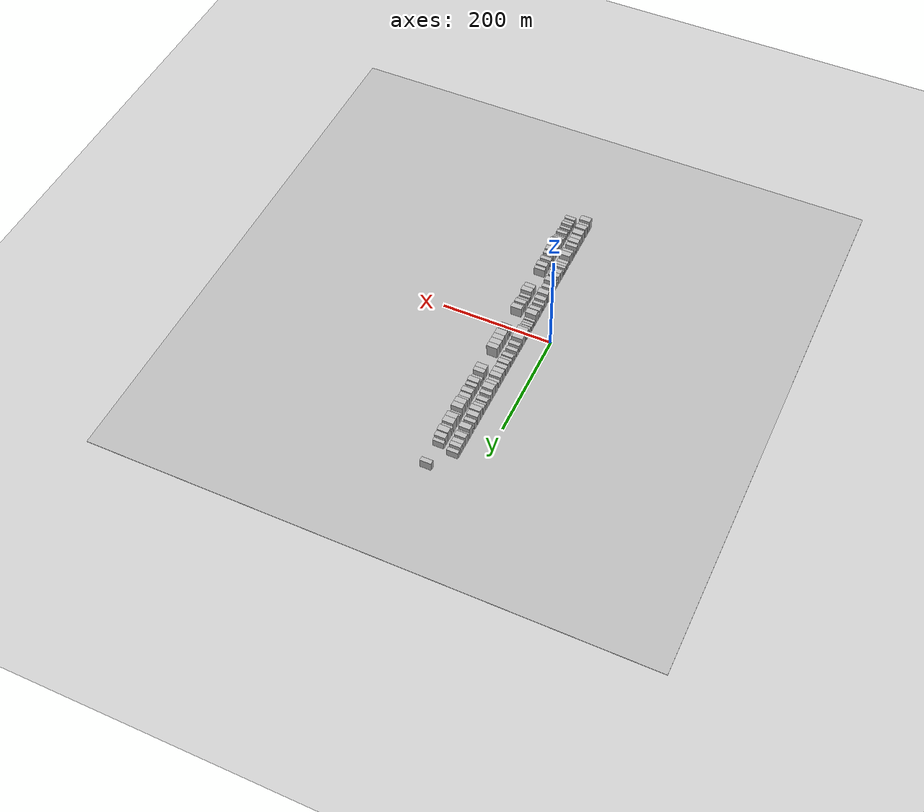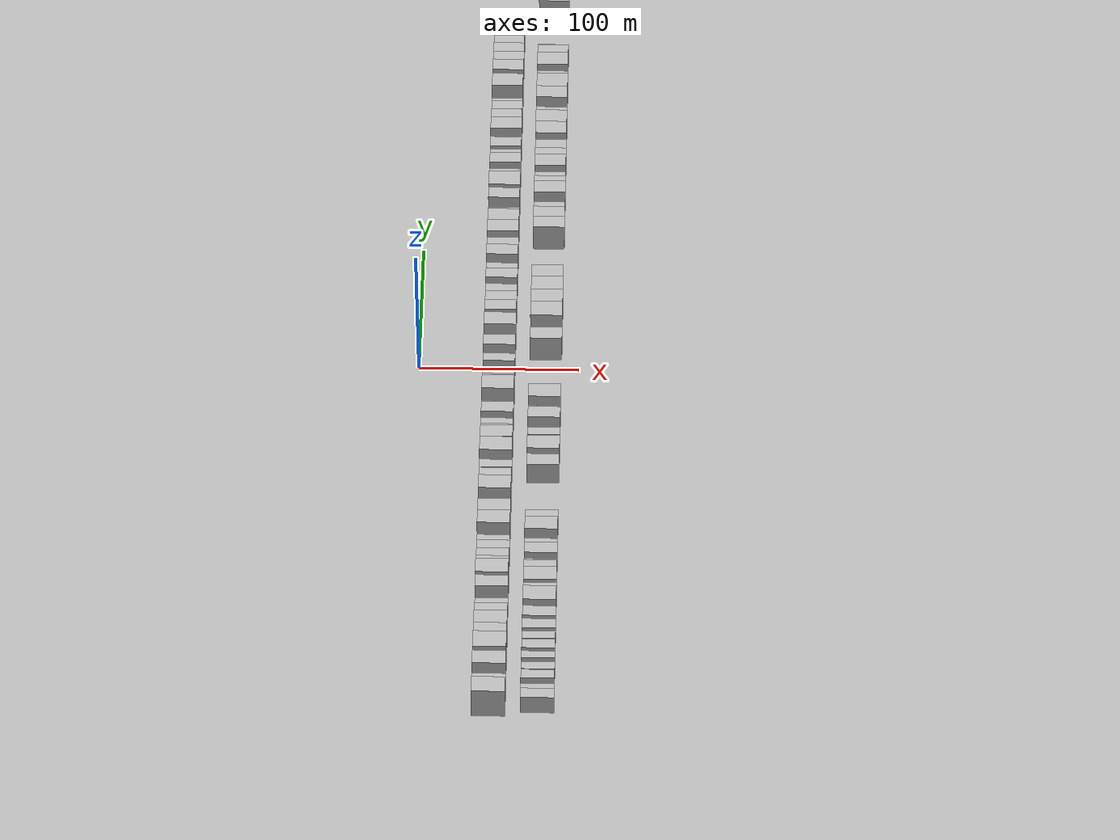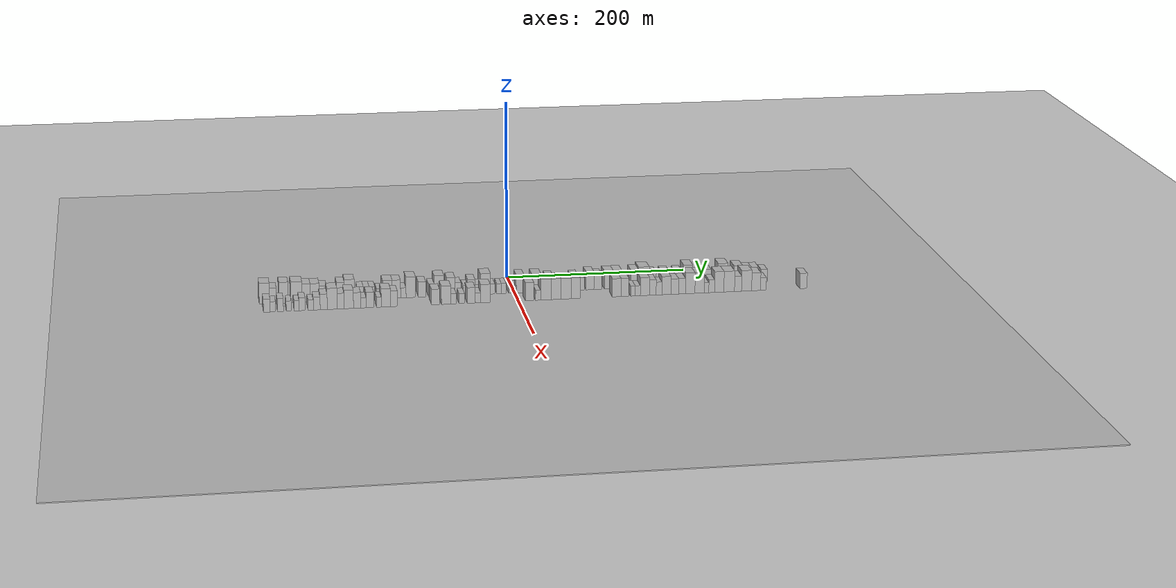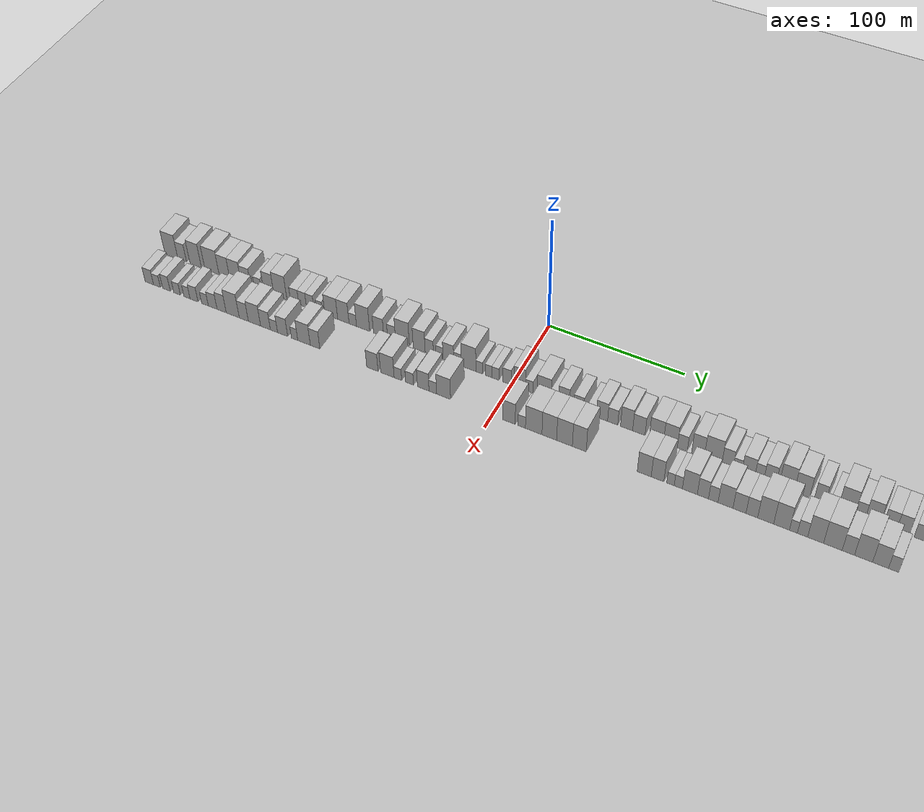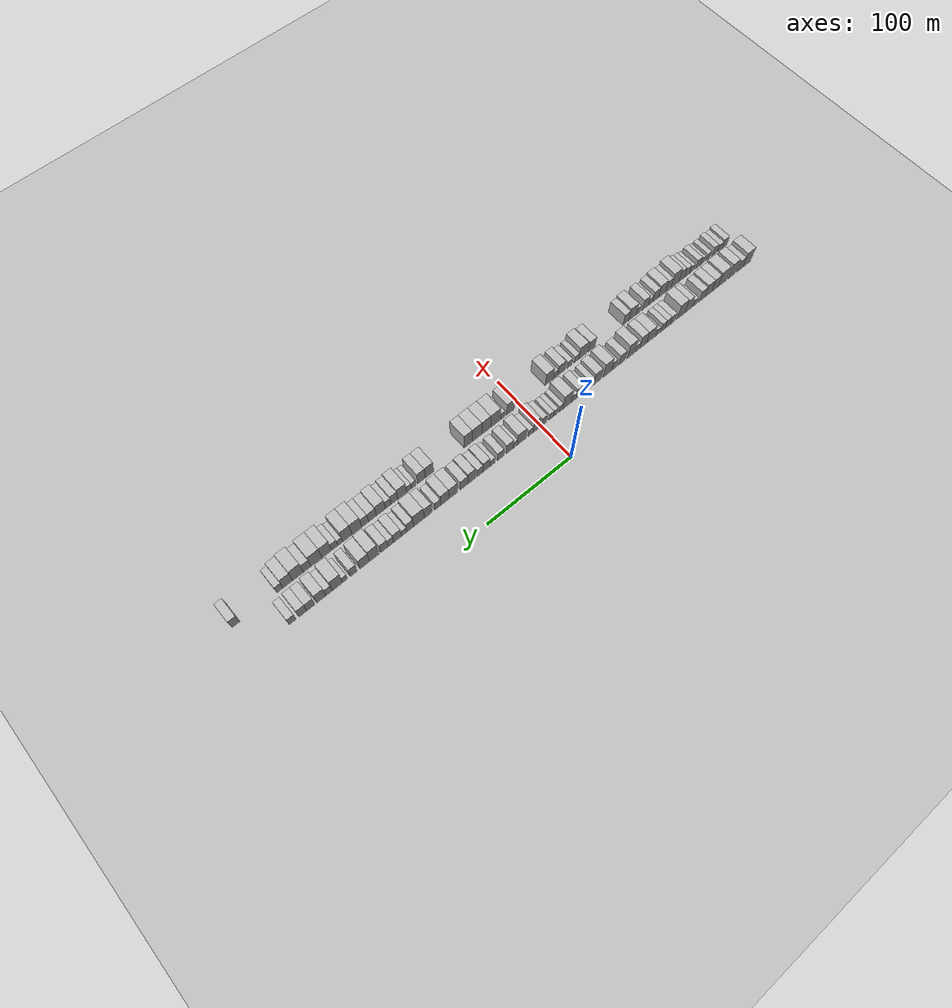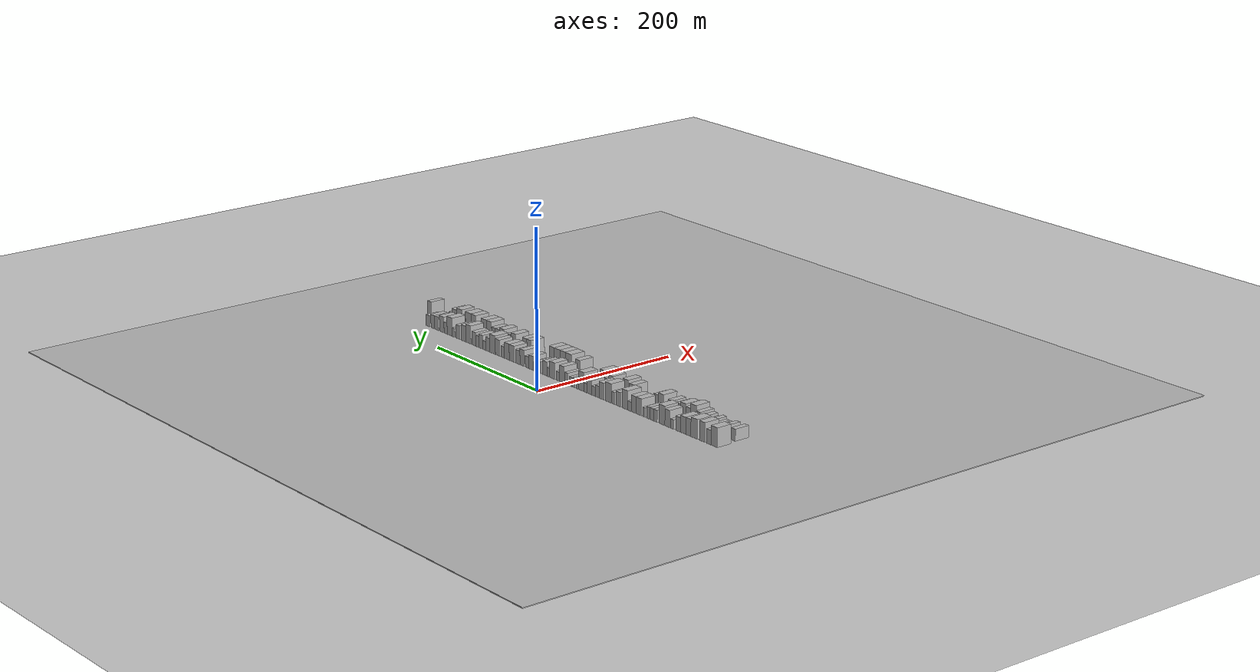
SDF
<?xml version="1.0" encoding="utf-8"?>

<sdf version="1.6">

   <world name="default">

      <gui fullscreen="0">

         <camera name="user_camera">

            <pose>-15 0 4.57585 0 0 0</pose>

            <view_controller>orbit</view_controller>

         </camera>

      </gui>

      <scene>

         <sky>

           <clouds>

             <speed>12</speed>

           </clouds>

         </sky>

         <ambient>0.4 0.4 0.4 1</ambient>

         <background>0.7 0.7 0.7 1</background>

         <shadows>1</shadows>

      </scene>

      <gravity>0 0 -9.8066</gravity>

      <magnetic_field>6e-06 2.3e-05 -4.2e-05</magnetic_field>

      <physics default="0" name="default_physics" type="ode">

         <ode>

            <solver>

               <type>quick</type>

               <iters>10</iters>

               <sor>1.0</sor>

               <use_dynamic_moi_rescaling>0</use_dynamic_moi_rescaling>

            </solver>

            <constraints>

               <cfm>0</cfm>

               <erp>0.2</erp>

               <contact_max_correcting_vel>100</contact_max_correcting_vel>

               <contact_surface_layer>0.001</contact_surface_layer>

            </constraints>

         </ode>

         <max_step_size>0.004</max_step_size>

         <real_time_factor>1</real_time_factor>

         <real_time_update_rate>250</real_time_update_rate>

      </physics>

      <light name="sun" type="directional">

         <cast_shadows>1</cast_shadows>

         <pose>0 0 10 0 0 0</pose>

         <diffuse>0.8 0.8 0.8 1</diffuse>

         <specular>0.2 0.2 0.2 1</specular>

         <attenuation>

            <range>1000</range>

            <constant>0.9</constant>

            <linear>0.01</linear>

            <quadratic>0.001</quadratic>

         </attenuation>

         <direction>-0.5 0.1 -0.9</direction>

      </light>

      <include>

         <name>ground_plane_1</name>

         <uri>model://HANNAS_ground_plane</uri>

         <pose>0 0 0  0 0 0</pose>

      </include>

      <include>

         <name>ground_plane_2</name>

         <uri>model://HANNAS_ground_plane</uri>

         <pose>100 0 0  0 0 0</pose>

      </include>

      <model name="building_1">

         <static>1</static>

         <pose frame="">50.0000 -272.4580 0 0.000000 0.000000 0.000000</pose>

         <link name="link">

            <pose frame="">0 0 12.00 0 0 0</pose>

            <collision name="collision">

               <geometry>

                  <box>

                     <size>20.0000 11.0839 24.0000</size>

                  </box>

               </geometry>

               <max_contacts>10</max_contacts>

               <surface>

                  <contact>

                     <ode/>

                  </contact>

                  <bounce/>

                  <friction>

                     <torsional>

                        <ode/>

                     </torsional>

                     <ode/>

                  </friction>

               </surface>

            </collision>

            <visual name="visual">

               <cast_shadows>0</cast_shadows>

               <geometry>

                  <box>

                     <size>20.0000 11.0839 24.0000</size>

                  </box>

               </geometry>

               <material>

                  <script>

                     <uri>model://HANNAS_wall/materials/scripts</uri>

                     <uri>model://HANNAS_wall/materials/textures</uri>

                     <name>vrc/HANNAS_wall</name>

                  </script>

               </material>

            </visual>

            <self_collide>0</self_collide>

            <enable_wind>0</enable_wind>

            <kinematic>0</kinematic>

         </link>

      </model>

      <model name="building_2">

         <static>1</static>

         <pose frame="">50.0000 -263.2071 0 0.000000 0.000000 0.000000</pose>

         <link name="link">

            <pose frame="">0 0 9.00 0 0 0</pose>

            <collision name="collision">

               <geometry>

                  <box>

                     <size>20.0000 7.4179 18.0000</size>

                  </box>

               </geometry>

               <max_contacts>10</max_contacts>

               <surface>

                  <contact>

                     <ode/>

                  </contact>

                  <bounce/>

                  <friction>

                     <torsional>

                        <ode/>

                     </torsional>

                     <ode/>

                  </friction>

               </surface>

            </collision>

            <visual name="visual">

               <cast_shadows>0</cast_shadows>

               <geometry>

                  <box>

                     <size>20.0000 7.4179 18.0000</size>

                  </box>

               </geometry>

               <material>

                  <script>

                     <uri>model://HANNAS_wall/materials/scripts</uri>

                     <uri>model://HANNAS_wall/materials/textures</uri>

                     <name>vrc/HANNAS_wall</name>

                  </script>

               </material>

            </visual>

            <self_collide>0</self_collide>

            <enable_wind>0</enable_wind>

            <kinematic>0</kinematic>

         </link>

      </model>

      <model name="building_3">

         <static>1</static>

         <pose frame="">50.0000 -251.6406 0 0.000000 0.000000 0.000000</pose>

         <link name="link">

            <pose frame="">0 0 12.00 0 0 0</pose>

            <collision name="collision">

               <geometry>

                  <box>

                     <size>20.0000 9.7152 24.0000</size>

                  </box>

               </geometry>

               <max_contacts>10</max_contacts>

               <surface>

                  <contact>

                     <ode/>

                  </contact>

                  <bounce/>

                  <friction>

                     <torsional>

                        <ode/>

                     </torsional>

                     <ode/>

                  </friction>

               </surface>

            </collision>

            <visual name="visual">

               <cast_shadows>0</cast_shadows>

               <geometry>

                  <box>

                     <size>20.0000 9.7152 24.0000</size>

                  </box>

               </geometry>

               <material>

                  <script>

                     <uri>model://HANNAS_wall/materials/scripts</uri>

                     <uri>model://HANNAS_wall/materials/textures</uri>

                     <name>vrc/HANNAS_wall</name>

                  </script>

               </material>

            </visual>

            <self_collide>0</self_collide>

            <enable_wind>0</enable_wind>

            <kinematic>0</kinematic>

         </link>

      </model>

      <model name="building_4">

         <static>1</static>

         <pose frame="">50.0000 -237.8133 0 0.000000 0.000000 0.000000</pose>

         <link name="link">

            <pose frame="">0 0 12.00 0 0 0</pose>

            <collision name="collision">

               <geometry>

                  <box>

                     <size>20.0000 11.9394 24.0000</size>

                  </box>

               </geometry>

               <max_contacts>10</max_contacts>

               <surface>

                  <contact>

                     <ode/>

                  </contact>

                  <bounce/>

                  <friction>

                     <torsional>

                        <ode/>

                     </torsional>

                     <ode/>

                  </friction>

               </surface>

            </collision>

            <visual name="visual">

               <cast_shadows>0</cast_shadows>

               <geometry>

                  <box>

                     <size>20.0000 11.9394 24.0000</size>

                  </box>

               </geometry>

               <material>

                  <script>

                     <uri>model://HANNAS_wall/materials/scripts</uri>

                     <uri>model://HANNAS_wall/materials/textures</uri>

                     <name>vrc/HANNAS_wall</name>

                  </script>

               </material>

            </visual>

            <self_collide>0</self_collide>

            <enable_wind>0</enable_wind>

            <kinematic>0</kinematic>

         </link>

      </model>

      <model name="building_5">

         <static>1</static>

         <pose frame="">50.0000 -227.3742 0 0.000000 0.000000 0.000000</pose>

         <link name="link">

            <pose frame="">0 0 10.50 0 0 0</pose>

            <collision name="collision">

               <geometry>

                  <box>

                     <size>20.0000 8.9388 21.0000</size>

                  </box>

               </geometry>

               <max_contacts>10</max_contacts>

               <surface>

                  <contact>

                     <ode/>

                  </contact>

                  <bounce/>

                  <friction>

                     <torsional>

                        <ode/>

                     </torsional>

                     <ode/>

                  </friction>

               </surface>

            </collision>

            <visual name="visual">

               <cast_shadows>0</cast_shadows>

               <geometry>

                  <box>

                     <size>20.0000 8.9388 21.0000</size>

                  </box>

               </geometry>

               <material>

                  <script>

                     <uri>model://HANNAS_wall/materials/scripts</uri>

                     <uri>model://HANNAS_wall/materials/textures</uri>

                     <name>vrc/HANNAS_wall</name>

                  </script>

               </material>

            </visual>

            <self_collide>0</self_collide>

            <enable_wind>0</enable_wind>

            <kinematic>0</kinematic>

         </link>

      </model>

      <model name="building_6">

         <static>1</static>

         <pose frame="">50.0000 -218.1332 0 0.000000 0.000000 0.000000</pose>

         <link name="link">

            <pose frame="">0 0 10.50 0 0 0</pose>

            <collision name="collision">

               <geometry>

                  <box>

                     <size>20.0000 9.5433 21.0000</size>

                  </box>

               </geometry>

               <max_contacts>10</max_contacts>

               <surface>

                  <contact>

                     <ode/>

                  </contact>

                  <bounce/>

                  <friction>

                     <torsional>

                        <ode/>

                     </torsional>

                     <ode/>

                  </friction>

               </surface>

            </collision>

            <visual name="visual">

               <cast_shadows>0</cast_shadows>

               <geometry>

                  <box>

                     <size>20.0000 9.5433 21.0000</size>

                  </box>

               </geometry>

               <material>

                  <script>

                     <uri>model://HANNAS_wall/materials/scripts</uri>

                     <uri>model://HANNAS_wall/materials/textures</uri>

                     <name>vrc/HANNAS_wall</name>

                  </script>

               </material>

            </visual>

            <self_collide>0</self_collide>

            <enable_wind>0</enable_wind>

            <kinematic>0</kinematic>

         </link>

      </model>

      <model name="building_7">

         <static>1</static>

         <pose frame="">50.0000 -209.2795 0 0.000000 0.000000 0.000000</pose>

         <link name="link">

            <pose frame="">0 0 9.00 0 0 0</pose>

            <collision name="collision">

               <geometry>

                  <box>

                     <size>20.0000 8.1641 18.0000</size>

                  </box>

               </geometry>

               <max_contacts>10</max_contacts>

               <surface>

                  <contact>

                     <ode/>

                  </contact>

                  <bounce/>

                  <friction>

                     <torsional>

                        <ode/>

                     </torsional>

                     <ode/>

                  </friction>

               </surface>

            </collision>

            <visual name="visual">

               <cast_shadows>0</cast_shadows>

               <geometry>

                  <box>

                     <size>20.0000 8.1641 18.0000</size>

                  </box>

               </geometry>

               <material>

                  <script>

                     <uri>model://HANNAS_wall/materials/scripts</uri>

                     <uri>model://HANNAS_wall/materials/textures</uri>

                     <name>vrc/HANNAS_wall</name>

                  </script>

               </material>

            </visual>

            <self_collide>0</self_collide>

            <enable_wind>0</enable_wind>

            <kinematic>0</kinematic>

         </link>

      </model>

      <model name="building_8">

         <static>1</static>

         <pose frame="">50.0000 -199.2894 0 0.000000 0.000000 0.000000</pose>

         <link name="link">

            <pose frame="">0 0 6.00 0 0 0</pose>

            <collision name="collision">

               <geometry>

                  <box>

                     <size>20.0000 5.8160 12.0000</size>

                  </box>

               </geometry>

               <max_contacts>10</max_contacts>

               <surface>

                  <contact>

                     <ode/>

                  </contact>

                  <bounce/>

                  <friction>

                     <torsional>

                        <ode/>

                     </torsional>

                     <ode/>

                  </friction>

               </surface>

            </collision>

            <visual name="visual">

               <cast_shadows>0</cast_shadows>

               <geometry>

                  <box>

                     <size>20.0000 5.8160 12.0000</size>

                  </box>

               </geometry>

               <material>

                  <script>

                     <uri>model://HANNAS_wall/materials/scripts</uri>

                     <uri>model://HANNAS_wall/materials/textures</uri>

                     <name>vrc/HANNAS_wall</name>

                  </script>

               </material>

            </visual>

            <self_collide>0</self_collide>

            <enable_wind>0</enable_wind>

            <kinematic>0</kinematic>

         </link>

      </model>

      <model name="building_9">

         <static>1</static>

         <pose frame="">50.0000 -190.1511 0 0.000000 0.000000 0.000000</pose>

         <link name="link">

            <pose frame="">0 0 10.50 0 0 0</pose>

            <collision name="collision">

               <geometry>

                  <box>

                     <size>20.0000 8.4607 21.0000</size>

                  </box>

               </geometry>

               <max_contacts>10</max_contacts>

               <surface>

                  <contact>

                     <ode/>

                  </contact>

                  <bounce/>

                  <friction>

                     <torsional>

                        <ode/>

                     </torsional>

                     <ode/>

                  </friction>

               </surface>

            </collision>

            <visual name="visual">

               <cast_shadows>0</cast_shadows>

               <geometry>

                  <box>

                     <size>20.0000 8.4607 21.0000</size>

                  </box>

               </geometry>

               <material>

                  <script>

                     <uri>model://HANNAS_wall/materials/scripts</uri>

                     <uri>model://HANNAS_wall/materials/textures</uri>

                     <name>vrc/HANNAS_wall</name>

                  </script>

               </material>

            </visual>

            <self_collide>0</self_collide>

            <enable_wind>0</enable_wind>

            <kinematic>0</kinematic>

         </link>

      </model>

      <model name="building_10">

         <static>1</static>

         <pose frame="">50.0000 -180.5715 0 0.000000 0.000000 0.000000</pose>

         <link name="link">

            <pose frame="">0 0 12.00 0 0 0</pose>

            <collision name="collision">

               <geometry>

                  <box>

                     <size>20.0000 10.6986 24.0000</size>

                  </box>

               </geometry>

               <max_contacts>10</max_contacts>

               <surface>

                  <contact>

                     <ode/>

                  </contact>

                  <bounce/>

                  <friction>

                     <torsional>

                        <ode/>

                     </torsional>

                     <ode/>

                  </friction>

               </surface>

            </collision>

            <visual name="visual">

               <cast_shadows>0</cast_shadows>

               <geometry>

                  <box>

                     <size>20.0000 10.6986 24.0000</size>

                  </box>

               </geometry>

               <material>

                  <script>

                     <uri>model://HANNAS_wall/materials/scripts</uri>

                     <uri>model://HANNAS_wall/materials/textures</uri>

                     <name>vrc/HANNAS_wall</name>

                  </script>

               </material>

            </visual>

            <self_collide>0</self_collide>

            <enable_wind>0</enable_wind>

            <kinematic>0</kinematic>

         </link>

      </model>

      <model name="building_11">

         <static>1</static>

         <pose frame="">50.0000 -168.8535 0 0.000000 0.000000 0.000000</pose>

         <link name="link">

            <pose frame="">0 0 7.50 0 0 0</pose>

            <collision name="collision">

               <geometry>

                  <box>

                     <size>20.0000 6.7373 15.0000</size>

                  </box>

               </geometry>

               <max_contacts>10</max_contacts>

               <surface>

                  <contact>

                     <ode/>

                  </contact>

                  <bounce/>

                  <friction>

                     <torsional>

                        <ode/>

                     </torsional>

                     <ode/>

                  </friction>

               </surface>

            </collision>

            <visual name="visual">

               <cast_shadows>0</cast_shadows>

               <geometry>

                  <box>

                     <size>20.0000 6.7373 15.0000</size>

                  </box>

               </geometry>

               <material>

                  <script>

                     <uri>model://HANNAS_wall/materials/scripts</uri>

                     <uri>model://HANNAS_wall/materials/textures</uri>

                     <name>vrc/HANNAS_wall</name>

                  </script>

               </material>

            </visual>

            <self_collide>0</self_collide>

            <enable_wind>0</enable_wind>

            <kinematic>0</kinematic>

         </link>

      </model>

      <model name="building_12">

         <static>1</static>

         <pose frame="">50.0000 -162.3870 0 0.000000 0.000000 0.000000</pose>

         <link name="link">

            <pose frame="">0 0 7.50 0 0 0</pose>

            <collision name="collision">

               <geometry>

                  <box>

                     <size>20.0000 6.1957 15.0000</size>

                  </box>

               </geometry>

               <max_contacts>10</max_contacts>

               <surface>

                  <contact>

                     <ode/>

                  </contact>

                  <bounce/>

                  <friction>

                     <torsional>

                        <ode/>

                     </torsional>

                     <ode/>

                  </friction>

               </surface>

            </collision>

            <visual name="visual">

               <cast_shadows>0</cast_shadows>

               <geometry>

                  <box>

                     <size>20.0000 6.1957 15.0000</size>

                  </box>

               </geometry>

               <material>

                  <script>

                     <uri>model://HANNAS_wall/materials/scripts</uri>

                     <uri>model://HANNAS_wall/materials/textures</uri>

                     <name>vrc/HANNAS_wall</name>

                  </script>

               </material>

            </visual>

            <self_collide>0</self_collide>

            <enable_wind>0</enable_wind>

            <kinematic>0</kinematic>

         </link>

      </model>

      <model name="building_13">

         <static>1</static>

         <pose frame="">50.0000 -156.2101 0 0.000000 0.000000 0.000000</pose>

         <link name="link">

            <pose frame="">0 0 7.50 0 0 0</pose>

            <collision name="collision">

               <geometry>

                  <box>

                     <size>20.0000 6.1582 15.0000</size>

                  </box>

               </geometry>

               <max_contacts>10</max_contacts>

               <surface>

                  <contact>

                     <ode/>

                  </contact>

                  <bounce/>

                  <friction>

                     <torsional>

                        <ode/>

                     </torsional>

                     <ode/>

                  </friction>

               </surface>

            </collision>

            <visual name="visual">

               <cast_shadows>0</cast_shadows>

               <geometry>

                  <box>

                     <size>20.0000 6.1582 15.0000</size>

                  </box>

               </geometry>

               <material>

                  <script>

                     <uri>model://HANNAS_wall/materials/scripts</uri>

                     <uri>model://HANNAS_wall/materials/textures</uri>

                     <name>vrc/HANNAS_wall</name>

                  </script>

               </material>

            </visual>

            <self_collide>0</self_collide>

            <enable_wind>0</enable_wind>

            <kinematic>0</kinematic>

         </link>

      </model>

      <model name="building_14">

         <static>1</static>

         <pose frame="">50.0000 -148.7292 0 0.000000 0.000000 0.000000</pose>

         <link name="link">

            <pose frame="">0 0 6.00 0 0 0</pose>

            <collision name="collision">

               <geometry>

                  <box>

                     <size>20.0000 4.8036 12.0000</size>

                  </box>

               </geometry>

               <max_contacts>10</max_contacts>

               <surface>

                  <contact>

                     <ode/>

                  </contact>

                  <bounce/>

                  <friction>

                     <torsional>

                        <ode/>

                     </torsional>

                     <ode/>

                  </friction>

               </surface>

            </collision>

            <visual name="visual">

               <cast_shadows>0</cast_shadows>

               <geometry>

                  <box>

                     <size>20.0000 4.8036 12.0000</size>

                  </box>

               </geometry>

               <material>

                  <script>

                     <uri>model://HANNAS_wall/materials/scripts</uri>

                     <uri>model://HANNAS_wall/materials/textures</uri>

                     <name>vrc/HANNAS_wall</name>

                  </script>

               </material>

            </visual>

            <self_collide>0</self_collide>

            <enable_wind>0</enable_wind>

            <kinematic>0</kinematic>

         </link>

      </model>

      <model name="building_15">

         <static>1</static>

         <pose frame="">50.0000 -139.2050 0 0.000000 0.000000 0.000000</pose>

         <link name="link">

            <pose frame="">0 0 10.50 0 0 0</pose>

            <collision name="collision">

               <geometry>

                  <box>

                     <size>20.0000 10.2449 21.0000</size>

                  </box>

               </geometry>

               <max_contacts>10</max_contacts>

               <surface>

                  <contact>

                     <ode/>

                  </contact>

                  <bounce/>

                  <friction>

                     <torsional>

                        <ode/>

                     </torsional>

                     <ode/>

                  </friction>

               </surface>

            </collision>

            <visual name="visual">

               <cast_shadows>0</cast_shadows>

               <geometry>

                  <box>

                     <size>20.0000 10.2449 21.0000</size>

                  </box>

               </geometry>

               <material>

                  <script>

                     <uri>model://HANNAS_wall/materials/scripts</uri>

                     <uri>model://HANNAS_wall/materials/textures</uri>

                     <name>vrc/HANNAS_wall</name>

                  </script>

               </material>

            </visual>

            <self_collide>0</self_collide>

            <enable_wind>0</enable_wind>

            <kinematic>0</kinematic>

         </link>

      </model>

      <model name="building_16">

         <static>1</static>

         <pose frame="">50.0000 -129.5559 0 0.000000 0.000000 0.000000</pose>

         <link name="link">

            <pose frame="">0 0 10.50 0 0 0</pose>

            <collision name="collision">

               <geometry>

                  <box>

                     <size>20.0000 9.0533 21.0000</size>

                  </box>

               </geometry>

               <max_contacts>10</max_contacts>

               <surface>

                  <contact>

                     <ode/>

                  </contact>

                  <bounce/>

                  <friction>

                     <torsional>

                        <ode/>

                     </torsional>

                     <ode/>

                  </friction>

               </surface>

            </collision>

            <visual name="visual">

               <cast_shadows>0</cast_shadows>

               <geometry>

                  <box>

                     <size>20.0000 9.0533 21.0000</size>

                  </box>

               </geometry>

               <material>

                  <script>

                     <uri>model://HANNAS_wall/materials/scripts</uri>

                     <uri>model://HANNAS_wall/materials/textures</uri>

                     <name>vrc/HANNAS_wall</name>

                  </script>

               </material>

            </visual>

            <self_collide>0</self_collide>

            <enable_wind>0</enable_wind>

            <kinematic>0</kinematic>

         </link>

      </model>

      <model name="building_17">

         <static>1</static>

         <pose frame="">50.0000 -122.0449 0 0.000000 0.000000 0.000000</pose>

         <link name="link">

            <pose frame="">0 0 6.00 0 0 0</pose>

            <collision name="collision">

               <geometry>

                  <box>

                     <size>20.0000 5.9686 12.0000</size>

                  </box>

               </geometry>

               <max_contacts>10</max_contacts>

               <surface>

                  <contact>

                     <ode/>

                  </contact>

                  <bounce/>

                  <friction>

                     <torsional>

                        <ode/>

                     </torsional>

                     <ode/>

                  </friction>

               </surface>

            </collision>

            <visual name="visual">

               <cast_shadows>0</cast_shadows>

               <geometry>

                  <box>

                     <size>20.0000 5.9686 12.0000</size>

                  </box>

               </geometry>

               <material>

                  <script>

                     <uri>model://HANNAS_wall/materials/scripts</uri>

                     <uri>model://HANNAS_wall/materials/textures</uri>

                     <name>vrc/HANNAS_wall</name>

                  </script>

               </material>

            </visual>

            <self_collide>0</self_collide>

            <enable_wind>0</enable_wind>

            <kinematic>0</kinematic>

         </link>

      </model>

      <model name="building_18">

         <static>1</static>

         <pose frame="">50.0000 -113.8500 0 0.000000 0.000000 0.000000</pose>

         <link name="link">

            <pose frame="">0 0 12.00 0 0 0</pose>

            <collision name="collision">

               <geometry>

                  <box>

                     <size>20.0000 10.4212 24.0000</size>

                  </box>

               </geometry>

               <max_contacts>10</max_contacts>

               <surface>

                  <contact>

                     <ode/>

                  </contact>

                  <bounce/>

                  <friction>

                     <torsional>

                        <ode/>

                     </torsional>

                     <ode/>

                  </friction>

               </surface>

            </collision>

            <visual name="visual">

               <cast_shadows>0</cast_shadows>

               <geometry>

                  <box>

                     <size>20.0000 10.4212 24.0000</size>

                  </box>

               </geometry>

               <material>

                  <script>

                     <uri>model://HANNAS_wall/materials/scripts</uri>

                     <uri>model://HANNAS_wall/materials/textures</uri>

                     <name>vrc/HANNAS_wall</name>

                  </script>

               </material>

            </visual>

            <self_collide>0</self_collide>

            <enable_wind>0</enable_wind>

            <kinematic>0</kinematic>

         </link>

      </model>

      <model name="building_19">

         <static>1</static>

         <pose frame="">50.0000 -101.5879 0 0.000000 0.000000 0.000000</pose>

         <link name="link">

            <pose frame="">0 0 9.00 0 0 0</pose>

            <collision name="collision">

               <geometry>

                  <box>

                     <size>20.0000 8.1029 18.0000</size>

                  </box>

               </geometry>

               <max_contacts>10</max_contacts>

               <surface>

                  <contact>

                     <ode/>

                  </contact>

                  <bounce/>

                  <friction>

                     <torsional>

                        <ode/>

                     </torsional>

                     <ode/>

                  </friction>

               </surface>

            </collision>

            <visual name="visual">

               <cast_shadows>0</cast_shadows>

               <geometry>

                  <box>

                     <size>20.0000 8.1029 18.0000</size>

                  </box>

               </geometry>

               <material>

                  <script>

                     <uri>model://HANNAS_wall/materials/scripts</uri>

                     <uri>model://HANNAS_wall/materials/textures</uri>

                     <name>vrc/HANNAS_wall</name>

                  </script>

               </material>

            </visual>

            <self_collide>0</self_collide>

            <enable_wind>0</enable_wind>

            <kinematic>0</kinematic>

         </link>

      </model>

      <model name="building_20">

         <static>1</static>

         <pose frame="">50.0000 -91.3871 0 0.000000 0.000000 0.000000</pose>

         <link name="link">

            <pose frame="">0 0 7.50 0 0 0</pose>

            <collision name="collision">

               <geometry>

                  <box>

                     <size>20.0000 6.2987 15.0000</size>

                  </box>

               </geometry>

               <max_contacts>10</max_contacts>

               <surface>

                  <contact>

                     <ode/>

                  </contact>

                  <bounce/>

                  <friction>

                     <torsional>

                        <ode/>

                     </torsional>

                     <ode/>

                  </friction>

               </surface>

            </collision>

            <visual name="visual">

               <cast_shadows>0</cast_shadows>

               <geometry>

                  <box>

                     <size>20.0000 6.2987 15.0000</size>

                  </box>

               </geometry>

               <material>

                  <script>

                     <uri>model://HANNAS_wall/materials/scripts</uri>

                     <uri>model://HANNAS_wall/materials/textures</uri>

                     <name>vrc/HANNAS_wall</name>

                  </script>

               </material>

            </visual>

            <self_collide>0</self_collide>

            <enable_wind>0</enable_wind>

            <kinematic>0</kinematic>

         </link>

      </model>

      <model name="building_21">

         <static>1</static>

         <pose frame="">50.0000 -82.8770 0 0.000000 0.000000 0.000000</pose>

         <link name="link">

            <pose frame="">0 0 12.00 0 0 0</pose>

            <collision name="collision">

               <geometry>

                  <box>

                     <size>20.0000 10.7214 24.0000</size>

                  </box>

               </geometry>

               <max_contacts>10</max_contacts>

               <surface>

                  <contact>

                     <ode/>

                  </contact>

                  <bounce/>

                  <friction>

                     <torsional>

                        <ode/>

                     </torsional>

                     <ode/>

                  </friction>

               </surface>

            </collision>

            <visual name="visual">

               <cast_shadows>0</cast_shadows>

               <geometry>

                  <box>

                     <size>20.0000 10.7214 24.0000</size>

                  </box>

               </geometry>

               <material>

                  <script>

                     <uri>model://HANNAS_wall/materials/scripts</uri>

                     <uri>model://HANNAS_wall/materials/textures</uri>

                     <name>vrc/HANNAS_wall</name>

                  </script>

               </material>

            </visual>

            <self_collide>0</self_collide>

            <enable_wind>0</enable_wind>

            <kinematic>0</kinematic>

         </link>

      </model>

      <model name="building_22">

         <static>1</static>

         <pose frame="">50.0000 -69.9177 0 0.000000 0.000000 0.000000</pose>

         <link name="link">

            <pose frame="">0 0 10.50 0 0 0</pose>

            <collision name="collision">

               <geometry>

                  <box>

                     <size>20.0000 9.1972 21.0000</size>

                  </box>

               </geometry>

               <max_contacts>10</max_contacts>

               <surface>

                  <contact>

                     <ode/>

                  </contact>

                  <bounce/>

                  <friction>

                     <torsional>

                        <ode/>

                     </torsional>

                     <ode/>

                  </friction>

               </surface>

            </collision>

            <visual name="visual">

               <cast_shadows>0</cast_shadows>

               <geometry>

                  <box>

                     <size>20.0000 9.1972 21.0000</size>

                  </box>

               </geometry>

               <material>

                  <script>

                     <uri>model://HANNAS_wall/materials/scripts</uri>

                     <uri>model://HANNAS_wall/materials/textures</uri>

                     <name>vrc/HANNAS_wall</name>

                  </script>

               </material>

            </visual>

            <self_collide>0</self_collide>

            <enable_wind>0</enable_wind>

            <kinematic>0</kinematic>

         </link>

      </model>

      <model name="building_23">

         <static>1</static>

         <pose frame="">50.0000 -62.0917 0 0.000000 0.000000 0.000000</pose>

         <link name="link">

            <pose frame="">0 0 7.50 0 0 0</pose>

            <collision name="collision">

               <geometry>

                  <box>

                     <size>20.0000 6.4550 15.0000</size>

                  </box>

               </geometry>

               <max_contacts>10</max_contacts>

               <surface>

                  <contact>

                     <ode/>

                  </contact>

                  <bounce/>

                  <friction>

                     <torsional>

                        <ode/>

                     </torsional>

                     <ode/>

                  </friction>

               </surface>

            </collision>

            <visual name="visual">

               <cast_shadows>0</cast_shadows>

               <geometry>

                  <box>

                     <size>20.0000 6.4550 15.0000</size>

                  </box>

               </geometry>

               <material>

                  <script>

                     <uri>model://HANNAS_wall/materials/scripts</uri>

                     <uri>model://HANNAS_wall/materials/textures</uri>

                     <name>vrc/HANNAS_wall</name>

                  </script>

               </material>

            </visual>

            <self_collide>0</self_collide>

            <enable_wind>0</enable_wind>

            <kinematic>0</kinematic>

         </link>

      </model>

      <model name="building_24">

         <static>1</static>

         <pose frame="">50.0000 -54.2108 0 0.000000 0.000000 0.000000</pose>

         <link name="link">

            <pose frame="">0 0 6.00 0 0 0</pose>

            <collision name="collision">

               <geometry>

                  <box>

                     <size>20.0000 5.3067 12.0000</size>

                  </box>

               </geometry>

               <max_contacts>10</max_contacts>

               <surface>

                  <contact>

                     <ode/>

                  </contact>

                  <bounce/>

                  <friction>

                     <torsional>

                        <ode/>

                     </torsional>

                     <ode/>

                  </friction>

               </surface>

            </collision>

            <visual name="visual">

               <cast_shadows>0</cast_shadows>

               <geometry>

                  <box>

                     <size>20.0000 5.3067 12.0000</size>

                  </box>

               </geometry>

               <material>

                  <script>

                     <uri>model://HANNAS_wall/materials/scripts</uri>

                     <uri>model://HANNAS_wall/materials/textures</uri>

                     <name>vrc/HANNAS_wall</name>

                  </script>

               </material>

            </visual>

            <self_collide>0</self_collide>

            <enable_wind>0</enable_wind>

            <kinematic>0</kinematic>

         </link>

      </model>

      <model name="building_25">

         <static>1</static>

         <pose frame="">50.0000 -47.4752 0 0.000000 0.000000 0.000000</pose>

         <link name="link">

            <pose frame="">0 0 9.00 0 0 0</pose>

            <collision name="collision">

               <geometry>

                  <box>

                     <size>20.0000 8.1644 18.0000</size>

                  </box>

               </geometry>

               <max_contacts>10</max_contacts>

               <surface>

                  <contact>

                     <ode/>

                  </contact>

                  <bounce/>

                  <friction>

                     <torsional>

                        <ode/>

                     </torsional>

                     <ode/>

                  </friction>

               </surface>

            </collision>

            <visual name="visual">

               <cast_shadows>0</cast_shadows>

               <geometry>

                  <box>

                     <size>20.0000 8.1644 18.0000</size>

                  </box>

               </geometry>

               <material>

                  <script>

                     <uri>model://HANNAS_wall/materials/scripts</uri>

                     <uri>model://HANNAS_wall/materials/textures</uri>

                     <name>vrc/HANNAS_wall</name>

                  </script>

               </material>

            </visual>

            <self_collide>0</self_collide>

            <enable_wind>0</enable_wind>

            <kinematic>0</kinematic>

         </link>

      </model>

      <model name="building_26">

         <static>1</static>

         <pose frame="">50.0000 -40.4975 0 0.000000 0.000000 0.000000</pose>

         <link name="link">

            <pose frame="">0 0 6.00 0 0 0</pose>

            <collision name="collision">

               <geometry>

                  <box>

                     <size>20.0000 5.7911 12.0000</size>

                  </box>

               </geometry>

               <max_contacts>10</max_contacts>

               <surface>

                  <contact>

                     <ode/>

                  </contact>

                  <bounce/>

                  <friction>

                     <torsional>

                        <ode/>

                     </torsional>

                     <ode/>

                  </friction>

               </surface>

            </collision>

            <visual name="visual">

               <cast_shadows>0</cast_shadows>

               <geometry>

                  <box>

                     <size>20.0000 5.7911 12.0000</size>

                  </box>

               </geometry>

               <material>

                  <script>

                     <uri>model://HANNAS_wall/materials/scripts</uri>

                     <uri>model://HANNAS_wall/materials/textures</uri>

                     <name>vrc/HANNAS_wall</name>

                  </script>

               </material>

            </visual>

            <self_collide>0</self_collide>

            <enable_wind>0</enable_wind>

            <kinematic>0</kinematic>

         </link>

      </model>

      <model name="building_27">

         <static>1</static>

         <pose frame="">50.0000 -32.0658 0 0.000000 0.000000 0.000000</pose>

         <link name="link">

            <pose frame="">0 0 12.00 0 0 0</pose>

            <collision name="collision">

               <geometry>

                  <box>

                     <size>20.0000 11.0724 24.0000</size>

                  </box>

               </geometry>

               <max_contacts>10</max_contacts>

               <surface>

                  <contact>

                     <ode/>

                  </contact>

                  <bounce/>

                  <friction>

                     <torsional>

                        <ode/>

                     </torsional>

                     <ode/>

                  </friction>

               </surface>

            </collision>

            <visual name="visual">

               <cast_shadows>0</cast_shadows>

               <geometry>

                  <box>

                     <size>20.0000 11.0724 24.0000</size>

                  </box>

               </geometry>

               <material>

                  <script>

                     <uri>model://HANNAS_wall/materials/scripts</uri>

                     <uri>model://HANNAS_wall/materials/textures</uri>

                     <name>vrc/HANNAS_wall</name>

                  </script>

               </material>

            </visual>

            <self_collide>0</self_collide>

            <enable_wind>0</enable_wind>

            <kinematic>0</kinematic>

         </link>

      </model>

      <model name="building_28">

         <static>1</static>

         <pose frame="">50.0000 -24.0606 0 0.000000 0.000000 0.000000</pose>

         <link name="link">

            <pose frame="">0 0 6.00 0 0 0</pose>

            <collision name="collision">

               <geometry>

                  <box>

                     <size>20.0000 4.9379 12.0000</size>

                  </box>

               </geometry>

               <max_contacts>10</max_contacts>

               <surface>

                  <contact>

                     <ode/>

                  </contact>

                  <bounce/>

                  <friction>

                     <torsional>

                        <ode/>

                     </torsional>

                     <ode/>

                  </friction>

               </surface>

            </collision>

            <visual name="visual">

               <cast_shadows>0</cast_shadows>

               <geometry>

                  <box>

                     <size>20.0000 4.9379 12.0000</size>

                  </box>

               </geometry>

               <material>

                  <script>

                     <uri>model://HANNAS_wall/materials/scripts</uri>

                     <uri>model://HANNAS_wall/materials/textures</uri>

                     <name>vrc/HANNAS_wall</name>

                  </script>

               </material>

            </visual>

            <self_collide>0</self_collide>

            <enable_wind>0</enable_wind>

            <kinematic>0</kinematic>

         </link>

      </model>

      <model name="building_29">

         <static>1</static>

         <pose frame="">50.0000 -17.1362 0 0.000000 0.000000 0.000000</pose>

         <link name="link">

            <pose frame="">0 0 6.00 0 0 0</pose>

            <collision name="collision">

               <geometry>

                  <box>

                     <size>20.0000 4.9109 12.0000</size>

                  </box>

               </geometry>

               <max_contacts>10</max_contacts>

               <surface>

                  <contact>

                     <ode/>

                  </contact>

                  <bounce/>

                  <friction>

                     <torsional>

                        <ode/>

                     </torsional>

                     <ode/>

                  </friction>

               </surface>

            </collision>

            <visual name="visual">

               <cast_shadows>0</cast_shadows>

               <geometry>

                  <box>

                     <size>20.0000 4.9109 12.0000</size>

                  </box>

               </geometry>

               <material>

                  <script>

                     <uri>model://HANNAS_wall/materials/scripts</uri>

                     <uri>model://HANNAS_wall/materials/textures</uri>

                     <name>vrc/HANNAS_wall</name>

                  </script>

               </material>

            </visual>

            <self_collide>0</self_collide>

            <enable_wind>0</enable_wind>

            <kinematic>0</kinematic>

         </link>

      </model>

      <model name="building_30">

         <static>1</static>

         <pose frame="">50.0000 -12.0396 0 0.000000 0.000000 0.000000</pose>

         <link name="link">

            <pose frame="">0 0 6.00 0 0 0</pose>

            <collision name="collision">

               <geometry>

                  <box>

                     <size>20.0000 5.2822 12.0000</size>

                  </box>

               </geometry>

               <max_contacts>10</max_contacts>

               <surface>

                  <contact>

                     <ode/>

                  </contact>

                  <bounce/>

                  <friction>

                     <torsional>

                        <ode/>

                     </torsional>

                     <ode/>

                  </friction>

               </surface>

            </collision>

            <visual name="visual">

               <cast_shadows>0</cast_shadows>

               <geometry>

                  <box>

                     <size>20.0000 5.2822 12.0000</size>

                  </box>

               </geometry>

               <material>

                  <script>

                     <uri>model://HANNAS_wall/materials/scripts</uri>

                     <uri>model://HANNAS_wall/materials/textures</uri>

                     <name>vrc/HANNAS_wall</name>

                  </script>

               </material>

            </visual>

            <self_collide>0</self_collide>

            <enable_wind>0</enable_wind>

            <kinematic>0</kinematic>

         </link>

      </model>

      <model name="building_31">

         <static>1</static>

         <pose frame="">50.0000 -3.2938 0 0.000000 0.000000 0.000000</pose>

         <link name="link">

            <pose frame="">0 0 7.50 0 0 0</pose>

            <collision name="collision">

               <geometry>

                  <box>

                     <size>20.0000 6.2094 15.0000</size>

                  </box>

               </geometry>

               <max_contacts>10</max_contacts>

               <surface>

                  <contact>

                     <ode/>

                  </contact>

                  <bounce/>

                  <friction>

                     <torsional>

                        <ode/>

                     </torsional>

                     <ode/>

                  </friction>

               </surface>

            </collision>

            <visual name="visual">

               <cast_shadows>0</cast_shadows>

               <geometry>

                  <box>

                     <size>20.0000 6.2094 15.0000</size>

                  </box>

               </geometry>

               <material>

                  <script>

                     <uri>model://HANNAS_wall/materials/scripts</uri>

                     <uri>model://HANNAS_wall/materials/textures</uri>

                     <name>vrc/HANNAS_wall</name>

                  </script>

               </material>

            </visual>

            <self_collide>0</self_collide>

            <enable_wind>0</enable_wind>

            <kinematic>0</kinematic>

         </link>

      </model>

      <model name="building_32">

         <static>1</static>

         <pose frame="">50.0000 6.1008 0 0.000000 0.000000 0.000000</pose>

         <link name="link">

            <pose frame="">0 0 10.50 0 0 0</pose>

            <collision name="collision">

               <geometry>

                  <box>

                     <size>20.0000 8.5798 21.0000</size>

                  </box>

               </geometry>

               <max_contacts>10</max_contacts>

               <surface>

                  <contact>

                     <ode/>

                  </contact>

                  <bounce/>

                  <friction>

                     <torsional>

                        <ode/>

                     </torsional>

                     <ode/>

                  </friction>

               </surface>

            </collision>

            <visual name="visual">

               <cast_shadows>0</cast_shadows>

               <geometry>

                  <box>

                     <size>20.0000 8.5798 21.0000</size>

                  </box>

               </geometry>

               <material>

                  <script>

                     <uri>model://HANNAS_wall/materials/scripts</uri>

                     <uri>model://HANNAS_wall/materials/textures</uri>

                     <name>vrc/HANNAS_wall</name>

                  </script>

               </material>

            </visual>

            <self_collide>0</self_collide>

            <enable_wind>0</enable_wind>

            <kinematic>0</kinematic>

         </link>

      </model>

      <model name="building_33">

         <static>1</static>

         <pose frame="">50.0000 13.1931 0 0.000000 0.000000 0.000000</pose>

         <link name="link">

            <pose frame="">0 0 6.00 0 0 0</pose>

            <collision name="collision">

               <geometry>

                  <box>

                     <size>20.0000 5.6048 12.0000</size>

                  </box>

               </geometry>

               <max_contacts>10</max_contacts>

               <surface>

                  <contact>

                     <ode/>

                  </contact>

                  <bounce/>

                  <friction>

                     <torsional>

                        <ode/>

                     </torsional>

                     <ode/>

                  </friction>

               </surface>

            </collision>

            <visual name="visual">

               <cast_shadows>0</cast_shadows>

               <geometry>

                  <box>

                     <size>20.0000 5.6048 12.0000</size>

                  </box>

               </geometry>

               <material>

                  <script>

                     <uri>model://HANNAS_wall/materials/scripts</uri>

                     <uri>model://HANNAS_wall/materials/textures</uri>

                     <name>vrc/HANNAS_wall</name>

                  </script>

               </material>

            </visual>

            <self_collide>0</self_collide>

            <enable_wind>0</enable_wind>

            <kinematic>0</kinematic>

         </link>

      </model>

      <model name="building_34">

         <static>1</static>

         <pose frame="">50.0000 24.0938 0 0.000000 0.000000 0.000000</pose>

         <link name="link">

            <pose frame="">0 0 10.50 0 0 0</pose>

            <collision name="collision">

               <geometry>

                  <box>

                     <size>20.0000 10.1967 21.0000</size>

                  </box>

               </geometry>

               <max_contacts>10</max_contacts>

               <surface>

                  <contact>

                     <ode/>

                  </contact>

                  <bounce/>

                  <friction>

                     <torsional>

                        <ode/>

                     </torsional>

                     <ode/>

                  </friction>

               </surface>

            </collision>

            <visual name="visual">

               <cast_shadows>0</cast_shadows>

               <geometry>

                  <box>

                     <size>20.0000 10.1967 21.0000</size>

                  </box>

               </geometry>

               <material>

                  <script>

                     <uri>model://HANNAS_wall/materials/scripts</uri>

                     <uri>model://HANNAS_wall/materials/textures</uri>

                     <name>vrc/HANNAS_wall</name>

                  </script>

               </material>

            </visual>

            <self_collide>0</self_collide>

            <enable_wind>0</enable_wind>

            <kinematic>0</kinematic>

         </link>

      </model>

      <model name="building_35">

         <static>1</static>

         <pose frame="">50.0000 31.8113 0 0.000000 0.000000 0.000000</pose>

         <link name="link">

            <pose frame="">0 0 6.00 0 0 0</pose>

            <collision name="collision">

               <geometry>

                  <box>

                     <size>20.0000 5.2383 12.0000</size>

                  </box>

               </geometry>

               <max_contacts>10</max_contacts>

               <surface>

                  <contact>

                     <ode/>

                  </contact>

                  <bounce/>

                  <friction>

                     <torsional>

                        <ode/>

                     </torsional>

                     <ode/>

                  </friction>

               </surface>

            </collision>

            <visual name="visual">

               <cast_shadows>0</cast_shadows>

               <geometry>

                  <box>

                     <size>20.0000 5.2383 12.0000</size>

                  </box>

               </geometry>

               <material>

                  <script>

                     <uri>model://HANNAS_wall/materials/scripts</uri>

                     <uri>model://HANNAS_wall/materials/textures</uri>

                     <name>vrc/HANNAS_wall</name>

                  </script>

               </material>

            </visual>

            <self_collide>0</self_collide>

            <enable_wind>0</enable_wind>

            <kinematic>0</kinematic>

         </link>

      </model>

      <model name="building_36">

         <static>1</static>

         <pose frame="">50.0000 38.5017 0 0.000000 0.000000 0.000000</pose>

         <link name="link">

            <pose frame="">0 0 9.00 0 0 0</pose>

            <collision name="collision">

               <geometry>

                  <box>

                     <size>20.0000 8.1425 18.0000</size>

                  </box>

               </geometry>

               <max_contacts>10</max_contacts>

               <surface>

                  <contact>

                     <ode/>

                  </contact>

                  <bounce/>

                  <friction>

                     <torsional>

                        <ode/>

                     </torsional>

                     <ode/>

                  </friction>

               </surface>

            </collision>

            <visual name="visual">

               <cast_shadows>0</cast_shadows>

               <geometry>

                  <box>

                     <size>20.0000 8.1425 18.0000</size>

                  </box>

               </geometry>

               <material>

                  <script>

                     <uri>model://HANNAS_wall/materials/scripts</uri>

                     <uri>model://HANNAS_wall/materials/textures</uri>

                     <name>vrc/HANNAS_wall</name>

                  </script>

               </material>

            </visual>

            <self_collide>0</self_collide>

            <enable_wind>0</enable_wind>

            <kinematic>0</kinematic>

         </link>

      </model>

      <model name="building_37">

         <static>1</static>

         <pose frame="">50.0000 49.2781 0 0.000000 0.000000 0.000000</pose>

         <link name="link">

            <pose frame="">0 0 7.50 0 0 0</pose>

            <collision name="collision">

               <geometry>

                  <box>

                     <size>20.0000 7.4103 15.0000</size>

                  </box>

               </geometry>

               <max_contacts>10</max_contacts>

               <surface>

                  <contact>

                     <ode/>

                  </contact>

                  <bounce/>

                  <friction>

                     <torsional>

                        <ode/>

                     </torsional>

                     <ode/>

                  </friction>

               </surface>

            </collision>

            <visual name="visual">

               <cast_shadows>0</cast_shadows>

               <geometry>

                  <box>

                     <size>20.0000 7.4103 15.0000</size>

                  </box>

               </geometry>

               <material>

                  <script>

                     <uri>model://HANNAS_wall/materials/scripts</uri>

                     <uri>model://HANNAS_wall/materials/textures</uri>

                     <name>vrc/HANNAS_wall</name>

                  </script>

               </material>

            </visual>

            <self_collide>0</self_collide>

            <enable_wind>0</enable_wind>

            <kinematic>0</kinematic>

         </link>

      </model>

      <model name="building_38">

         <static>1</static>

         <pose frame="">50.0000 58.9026 0 0.000000 0.000000 0.000000</pose>

         <link name="link">

            <pose frame="">0 0 6.00 0 0 0</pose>

            <collision name="collision">

               <geometry>

                  <box>

                     <size>20.0000 5.8385 12.0000</size>

                  </box>

               </geometry>

               <max_contacts>10</max_contacts>

               <surface>

                  <contact>

                     <ode/>

                  </contact>

                  <bounce/>

                  <friction>

                     <torsional>

                        <ode/>

                     </torsional>

                     <ode/>

                  </friction>

               </surface>

            </collision>

            <visual name="visual">

               <cast_shadows>0</cast_shadows>

               <geometry>

                  <box>

                     <size>20.0000 5.8385 12.0000</size>

                  </box>

               </geometry>

               <material>

                  <script>

                     <uri>model://HANNAS_wall/materials/scripts</uri>

                     <uri>model://HANNAS_wall/materials/textures</uri>

                     <name>vrc/HANNAS_wall</name>

                  </script>

               </material>

            </visual>

            <self_collide>0</self_collide>

            <enable_wind>0</enable_wind>

            <kinematic>0</kinematic>

         </link>

      </model>

      <model name="building_39">

         <static>1</static>

         <pose frame="">50.0000 65.9199 0 0.000000 0.000000 0.000000</pose>

         <link name="link">

            <pose frame="">0 0 9.00 0 0 0</pose>

            <collision name="collision">

               <geometry>

                  <box>

                     <size>20.0000 8.1960 18.0000</size>

                  </box>

               </geometry>

               <max_contacts>10</max_contacts>

               <surface>

                  <contact>

                     <ode/>

                  </contact>

                  <bounce/>

                  <friction>

                     <torsional>

                        <ode/>

                     </torsional>

                     <ode/>

                  </friction>

               </surface>

            </collision>

            <visual name="visual">

               <cast_shadows>0</cast_shadows>

               <geometry>

                  <box>

                     <size>20.0000 8.1960 18.0000</size>

                  </box>

               </geometry>

               <material>

                  <script>

                     <uri>model://HANNAS_wall/materials/scripts</uri>

                     <uri>model://HANNAS_wall/materials/textures</uri>

                     <name>vrc/HANNAS_wall</name>

                  </script>

               </material>

            </visual>

            <self_collide>0</self_collide>

            <enable_wind>0</enable_wind>

            <kinematic>0</kinematic>

         </link>

      </model>

      <model name="building_40">

         <static>1</static>

         <pose frame="">50.0000 73.6145 0 0.000000 0.000000 0.000000</pose>

         <link name="link">

            <pose frame="">0 0 7.50 0 0 0</pose>

            <collision name="collision">

               <geometry>

                  <box>

                     <size>20.0000 7.1932 15.0000</size>

                  </box>

               </geometry>

               <max_contacts>10</max_contacts>

               <surface>

                  <contact>

                     <ode/>

                  </contact>

                  <bounce/>

                  <friction>

                     <torsional>

                        <ode/>

                     </torsional>

                     <ode/>

                  </friction>

               </surface>

            </collision>

            <visual name="visual">

               <cast_shadows>0</cast_shadows>

               <geometry>

                  <box>

                     <size>20.0000 7.1932 15.0000</size>

                  </box>

               </geometry>

               <material>

                  <script>

                     <uri>model://HANNAS_wall/materials/scripts</uri>

                     <uri>model://HANNAS_wall/materials/textures</uri>

                     <name>vrc/HANNAS_wall</name>

                  </script>

               </material>

            </visual>

            <self_collide>0</self_collide>

            <enable_wind>0</enable_wind>

            <kinematic>0</kinematic>

         </link>

      </model>

      <model name="building_41">

         <static>1</static>

         <pose frame="">50.0000 83.5099 0 0.000000 0.000000 0.000000</pose>

         <link name="link">

            <pose frame="">0 0 10.50 0 0 0</pose>

            <collision name="collision">

               <geometry>

                  <box>

                     <size>20.0000 8.5977 21.0000</size>

                  </box>

               </geometry>

               <max_contacts>10</max_contacts>

               <surface>

                  <contact>

                     <ode/>

                  </contact>

                  <bounce/>

                  <friction>

                     <torsional>

                        <ode/>

                     </torsional>

                     <ode/>

                  </friction>

               </surface>

            </collision>

            <visual name="visual">

               <cast_shadows>0</cast_shadows>

               <geometry>

                  <box>

                     <size>20.0000 8.5977 21.0000</size>

                  </box>

               </geometry>

               <material>

                  <script>

                     <uri>model://HANNAS_wall/materials/scripts</uri>

                     <uri>model://HANNAS_wall/materials/textures</uri>

                     <name>vrc/HANNAS_wall</name>

                  </script>

               </material>

            </visual>

            <self_collide>0</self_collide>

            <enable_wind>0</enable_wind>

            <kinematic>0</kinematic>

         </link>

      </model>

      <model name="building_42">

         <static>1</static>

         <pose frame="">50.0000 92.1549 0 0.000000 0.000000 0.000000</pose>

         <link name="link">

            <pose frame="">0 0 9.00 0 0 0</pose>

            <collision name="collision">

               <geometry>

                  <box>

                     <size>20.0000 8.6923 18.0000</size>

                  </box>

               </geometry>

               <max_contacts>10</max_contacts>

               <surface>

                  <contact>

                     <ode/>

                  </contact>

                  <bounce/>

                  <friction>

                     <torsional>

                        <ode/>

                     </torsional>

                     <ode/>

                  </friction>

               </surface>

            </collision>

            <visual name="visual">

               <cast_shadows>0</cast_shadows>

               <geometry>

                  <box>

                     <size>20.0000 8.6923 18.0000</size>

                  </box>

               </geometry>

               <material>

                  <script>

                     <uri>model://HANNAS_wall/materials/scripts</uri>

                     <uri>model://HANNAS_wall/materials/textures</uri>

                     <name>vrc/HANNAS_wall</name>

                  </script>

               </material>

            </visual>

            <self_collide>0</self_collide>

            <enable_wind>0</enable_wind>

            <kinematic>0</kinematic>

         </link>

      </model>

      <model name="building_43">

         <static>1</static>

         <pose frame="">50.0000 104.4483 0 0.000000 0.000000 0.000000</pose>

         <link name="link">

            <pose frame="">0 0 10.50 0 0 0</pose>

            <collision name="collision">

               <geometry>

                  <box>

                     <size>20.0000 9.8944 21.0000</size>

                  </box>

               </geometry>

               <max_contacts>10</max_contacts>

               <surface>

                  <contact>

                     <ode/>

                  </contact>

                  <bounce/>

                  <friction>

                     <torsional>

                        <ode/>

                     </torsional>

                     <ode/>

                  </friction>

               </surface>

            </collision>

            <visual name="visual">

               <cast_shadows>0</cast_shadows>

               <geometry>

                  <box>

                     <size>20.0000 9.8944 21.0000</size>

                  </box>

               </geometry>

               <material>

                  <script>

                     <uri>model://HANNAS_wall/materials/scripts</uri>

                     <uri>model://HANNAS_wall/materials/textures</uri>

                     <name>vrc/HANNAS_wall</name>

                  </script>

               </material>

            </visual>

            <self_collide>0</self_collide>

            <enable_wind>0</enable_wind>

            <kinematic>0</kinematic>

         </link>

      </model>

      <model name="building_44">

         <static>1</static>

         <pose frame="">50.0000 114.1976 0 0.000000 0.000000 0.000000</pose>

         <link name="link">

            <pose frame="">0 0 10.50 0 0 0</pose>

            <collision name="collision">

               <geometry>

                  <box>

                     <size>20.0000 9.6041 21.0000</size>

                  </box>

               </geometry>

               <max_contacts>10</max_contacts>

               <surface>

                  <contact>

                     <ode/>

                  </contact>

                  <bounce/>

                  <friction>

                     <torsional>

                        <ode/>

                     </torsional>

                     <ode/>

                  </friction>

               </surface>

            </collision>

            <visual name="visual">

               <cast_shadows>0</cast_shadows>

               <geometry>

                  <box>

                     <size>20.0000 9.6041 21.0000</size>

                  </box>

               </geometry>

               <material>

                  <script>

                     <uri>model://HANNAS_wall/materials/scripts</uri>

                     <uri>model://HANNAS_wall/materials/textures</uri>

                     <name>vrc/HANNAS_wall</name>

                  </script>

               </material>

            </visual>

            <self_collide>0</self_collide>

            <enable_wind>0</enable_wind>

            <kinematic>0</kinematic>

         </link>

      </model>

      <model name="building_45">

         <static>1</static>

         <pose frame="">50.0000 122.4412 0 0.000000 0.000000 0.000000</pose>

         <link name="link">

            <pose frame="">0 0 7.50 0 0 0</pose>

            <collision name="collision">

               <geometry>

                  <box>

                     <size>20.0000 6.8831 15.0000</size>

                  </box>

               </geometry>

               <max_contacts>10</max_contacts>

               <surface>

                  <contact>

                     <ode/>

                  </contact>

                  <bounce/>

                  <friction>

                     <torsional>

                        <ode/>

                     </torsional>

                     <ode/>

                  </friction>

               </surface>

            </collision>

            <visual name="visual">

               <cast_shadows>0</cast_shadows>

               <geometry>

                  <box>

                     <size>20.0000 6.8831 15.0000</size>

                  </box>

               </geometry>

               <material>

                  <script>

                     <uri>model://HANNAS_wall/materials/scripts</uri>

                     <uri>model://HANNAS_wall/materials/textures</uri>

                     <name>vrc/HANNAS_wall</name>

                  </script>

               </material>

            </visual>

            <self_collide>0</self_collide>

            <enable_wind>0</enable_wind>

            <kinematic>0</kinematic>

         </link>

      </model>

      <model name="building_46">

         <static>1</static>

         <pose frame="">50.0000 133.2129 0 0.000000 0.000000 0.000000</pose>

         <link name="link">

            <pose frame="">0 0 10.50 0 0 0</pose>

            <collision name="collision">

               <geometry>

                  <box>

                     <size>20.0000 8.6603 21.0000</size>

                  </box>

               </geometry>

               <max_contacts>10</max_contacts>

               <surface>

                  <contact>

                     <ode/>

                  </contact>

                  <bounce/>

                  <friction>

                     <torsional>

                        <ode/>

                     </torsional>

                     <ode/>

                  </friction>

               </surface>

            </collision>

            <visual name="visual">

               <cast_shadows>0</cast_shadows>

               <geometry>

                  <box>

                     <size>20.0000 8.6603 21.0000</size>

                  </box>

               </geometry>

               <material>

                  <script>

                     <uri>model://HANNAS_wall/materials/scripts</uri>

                     <uri>model://HANNAS_wall/materials/textures</uri>

                     <name>vrc/HANNAS_wall</name>

                  </script>

               </material>

            </visual>

            <self_collide>0</self_collide>

            <enable_wind>0</enable_wind>

            <kinematic>0</kinematic>

         </link>

      </model>

      <model name="building_47">

         <static>1</static>

         <pose frame="">50.0000 143.5383 0 0.000000 0.000000 0.000000</pose>

         <link name="link">

            <pose frame="">0 0 12.00 0 0 0</pose>

            <collision name="collision">

               <geometry>

                  <box>

                     <size>20.0000 11.9904 24.0000</size>

                  </box>

               </geometry>

               <max_contacts>10</max_contacts>

               <surface>

                  <contact>

                     <ode/>

                  </contact>

                  <bounce/>

                  <friction>

                     <torsional>

                        <ode/>

                     </torsional>

                     <ode/>

                  </friction>

               </surface>

            </collision>

            <visual name="visual">

               <cast_shadows>0</cast_shadows>

               <geometry>

                  <box>

                     <size>20.0000 11.9904 24.0000</size>

                  </box>

               </geometry>

               <material>

                  <script>

                     <uri>model://HANNAS_wall/materials/scripts</uri>

                     <uri>model://HANNAS_wall/materials/textures</uri>

                     <name>vrc/HANNAS_wall</name>

                  </script>

               </material>

            </visual>

            <self_collide>0</self_collide>

            <enable_wind>0</enable_wind>

            <kinematic>0</kinematic>

         </link>

      </model>

      <model name="building_48">

         <static>1</static>

         <pose frame="">50.0000 153.3709 0 0.000000 0.000000 0.000000</pose>

         <link name="link">

            <pose frame="">0 0 9.00 0 0 0</pose>

            <collision name="collision">

               <geometry>

                  <box>

                     <size>20.0000 7.6747 18.0000</size>

                  </box>

               </geometry>

               <max_contacts>10</max_contacts>

               <surface>

                  <contact>

                     <ode/>

                  </contact>

                  <bounce/>

                  <friction>

                     <torsional>

                        <ode/>

                     </torsional>

                     <ode/>

                  </friction>

               </surface>

            </collision>

            <visual name="visual">

               <cast_shadows>0</cast_shadows>

               <geometry>

                  <box>

                     <size>20.0000 7.6747 18.0000</size>

                  </box>

               </geometry>

               <material>

                  <script>

                     <uri>model://HANNAS_wall/materials/scripts</uri>

                     <uri>model://HANNAS_wall/materials/textures</uri>

                     <name>vrc/HANNAS_wall</name>

                  </script>

               </material>

            </visual>

            <self_collide>0</self_collide>

            <enable_wind>0</enable_wind>

            <kinematic>0</kinematic>

         </link>

      </model>

      <model name="building_49">

         <static>1</static>

         <pose frame="">50.0000 160.1628 0 0.000000 0.000000 0.000000</pose>

         <link name="link">

            <pose frame="">0 0 6.00 0 0 0</pose>

            <collision name="collision">

               <geometry>

                  <box>

                     <size>20.0000 5.9092 12.0000</size>

                  </box>

               </geometry>

               <max_contacts>10</max_contacts>

               <surface>

                  <contact>

                     <ode/>

                  </contact>

                  <bounce/>

                  <friction>

                     <torsional>

                        <ode/>

                     </torsional>

                     <ode/>

                  </friction>

               </surface>

            </collision>

            <visual name="visual">

               <cast_shadows>0</cast_shadows>

               <geometry>

                  <box>

                     <size>20.0000 5.9092 12.0000</size>

                  </box>

               </geometry>

               <material>

                  <script>

                     <uri>model://HANNAS_wall/materials/scripts</uri>

                     <uri>model://HANNAS_wall/materials/textures</uri>

                     <name>vrc/HANNAS_wall</name>

                  </script>

               </material>

            </visual>

            <self_collide>0</self_collide>

            <enable_wind>0</enable_wind>

            <kinematic>0</kinematic>

         </link>

      </model>

      <model name="building_50">

         <static>1</static>

         <pose frame="">50.0000 167.4937 0 0.000000 0.000000 0.000000</pose>

         <link name="link">

            <pose frame="">0 0 9.00 0 0 0</pose>

            <collision name="collision">

               <geometry>

                  <box>

                     <size>20.0000 8.7525 18.0000</size>

                  </box>

               </geometry>

               <max_contacts>10</max_contacts>

               <surface>

                  <contact>

                     <ode/>

                  </contact>

                  <bounce/>

                  <friction>

                     <torsional>

                        <ode/>

                     </torsional>

                     <ode/>

                  </friction>

               </surface>

            </collision>

            <visual name="visual">

               <cast_shadows>0</cast_shadows>

               <geometry>

                  <box>

                     <size>20.0000 8.7525 18.0000</size>

                  </box>

               </geometry>

               <material>

                  <script>

                     <uri>model://HANNAS_wall/materials/scripts</uri>

                     <uri>model://HANNAS_wall/materials/textures</uri>

                     <name>vrc/HANNAS_wall</name>

                  </script>

               </material>

            </visual>

            <self_collide>0</self_collide>

            <enable_wind>0</enable_wind>

            <kinematic>0</kinematic>

         </link>

      </model>

      <model name="building_51">

         <static>1</static>

         <pose frame="">50.0000 174.8730 0 0.000000 0.000000 0.000000</pose>

         <link name="link">

            <pose frame="">0 0 7.50 0 0 0</pose>

            <collision name="collision">

               <geometry>

                  <box>

                     <size>20.0000 6.0060 15.0000</size>

                  </box>

               </geometry>

               <max_contacts>10</max_contacts>

               <surface>

                  <contact>

                     <ode/>

                  </contact>

                  <bounce/>

                  <friction>

                     <torsional>

                        <ode/>

                     </torsional>

                     <ode/>

                  </friction>

               </surface>

            </collision>

            <visual name="visual">

               <cast_shadows>0</cast_shadows>

               <geometry>

                  <box>

                     <size>20.0000 6.0060 15.0000</size>

                  </box>

               </geometry>

               <material>

                  <script>

                     <uri>model://HANNAS_wall/materials/scripts</uri>

                     <uri>model://HANNAS_wall/materials/textures</uri>

                     <name>vrc/HANNAS_wall</name>

                  </script>

               </material>

            </visual>

            <self_collide>0</self_collide>

            <enable_wind>0</enable_wind>

            <kinematic>0</kinematic>

         </link>

      </model>

      <model name="building_52">

         <static>1</static>

         <pose frame="">50.0000 181.9415 0 0.000000 0.000000 0.000000</pose>

         <link name="link">

            <pose frame="">0 0 9.00 0 0 0</pose>

            <collision name="collision">

               <geometry>

                  <box>

                     <size>20.0000 8.1310 18.0000</size>

                  </box>

               </geometry>

               <max_contacts>10</max_contacts>

               <surface>

                  <contact>

                     <ode/>

                  </contact>

                  <bounce/>

                  <friction>

                     <torsional>

                        <ode/>

                     </torsional>

                     <ode/>

                  </friction>

               </surface>

            </collision>

            <visual name="visual">

               <cast_shadows>0</cast_shadows>

               <geometry>

                  <box>

                     <size>20.0000 8.1310 18.0000</size>

                  </box>

               </geometry>

               <material>

                  <script>

                     <uri>model://HANNAS_wall/materials/scripts</uri>

                     <uri>model://HANNAS_wall/materials/textures</uri>

                     <name>vrc/HANNAS_wall</name>

                  </script>

               </material>

            </visual>

            <self_collide>0</self_collide>

            <enable_wind>0</enable_wind>

            <kinematic>0</kinematic>

         </link>

      </model>

      <model name="building_53">

         <static>1</static>

         <pose frame="">50.0000 193.0817 0 0.000000 0.000000 0.000000</pose>

         <link name="link">

            <pose frame="">0 0 12.00 0 0 0</pose>

            <collision name="collision">

               <geometry>

                  <box>

                     <size>20.0000 10.1494 24.0000</size>

                  </box>

               </geometry>

               <max_contacts>10</max_contacts>

               <surface>

                  <contact>

                     <ode/>

                  </contact>

                  <bounce/>

                  <friction>

                     <torsional>

                        <ode/>

                     </torsional>

                     <ode/>

                  </friction>

               </surface>

            </collision>

            <visual name="visual">

               <cast_shadows>0</cast_shadows>

               <geometry>

                  <box>

                     <size>20.0000 10.1494 24.0000</size>

                  </box>

               </geometry>

               <material>

                  <script>

                     <uri>model://HANNAS_wall/materials/scripts</uri>

                     <uri>model://HANNAS_wall/materials/textures</uri>

                     <name>vrc/HANNAS_wall</name>

                  </script>

               </material>

            </visual>

            <self_collide>0</self_collide>

            <enable_wind>0</enable_wind>

            <kinematic>0</kinematic>

         </link>

      </model>

      <model name="building_54">

         <static>1</static>

         <pose frame="">50.0000 203.2365 0 0.000000 0.000000 0.000000</pose>

         <link name="link">

            <pose frame="">0 0 10.50 0 0 0</pose>

            <collision name="collision">

               <geometry>

                  <box>

                     <size>20.0000 10.1603 21.0000</size>

                  </box>

               </geometry>

               <max_contacts>10</max_contacts>

               <surface>

                  <contact>

                     <ode/>

                  </contact>

                  <bounce/>

                  <friction>

                     <torsional>

                        <ode/>

                     </torsional>

                     <ode/>

                  </friction>

               </surface>

            </collision>

            <visual name="visual">

               <cast_shadows>0</cast_shadows>

               <geometry>

                  <box>

                     <size>20.0000 10.1603 21.0000</size>

                  </box>

               </geometry>

               <material>

                  <script>

                     <uri>model://HANNAS_wall/materials/scripts</uri>

                     <uri>model://HANNAS_wall/materials/textures</uri>

                     <name>vrc/HANNAS_wall</name>

                  </script>

               </material>

            </visual>

            <self_collide>0</self_collide>

            <enable_wind>0</enable_wind>

            <kinematic>0</kinematic>

         </link>

      </model>

      <model name="building_55">

         <static>1</static>

         <pose frame="">50.0000 215.0271 0 0.000000 0.000000 0.000000</pose>

         <link name="link">

            <pose frame="">0 0 9.00 0 0 0</pose>

            <collision name="collision">

               <geometry>

                  <box>

                     <size>20.0000 7.4208 18.0000</size>

                  </box>

               </geometry>

               <max_contacts>10</max_contacts>

               <surface>

                  <contact>

                     <ode/>

                  </contact>

                  <bounce/>

                  <friction>

                     <torsional>

                        <ode/>

                     </torsional>

                     <ode/>

                  </friction>

               </surface>

            </collision>

            <visual name="visual">

               <cast_shadows>0</cast_shadows>

               <geometry>

                  <box>

                     <size>20.0000 7.4208 18.0000</size>

                  </box>

               </geometry>

               <material>

                  <script>

                     <uri>model://HANNAS_wall/materials/scripts</uri>

                     <uri>model://HANNAS_wall/materials/textures</uri>

                     <name>vrc/HANNAS_wall</name>

                  </script>

               </material>

            </visual>

            <self_collide>0</self_collide>

            <enable_wind>0</enable_wind>

            <kinematic>0</kinematic>

         </link>

      </model>

      <model name="building_56">

         <static>1</static>

         <pose frame="">50.0000 224.3459 0 0.000000 0.000000 0.000000</pose>

         <link name="link">

            <pose frame="">0 0 6.00 0 0 0</pose>

            <collision name="collision">

               <geometry>

                  <box>

                     <size>20.0000 5.2167 12.0000</size>

                  </box>

               </geometry>

               <max_contacts>10</max_contacts>

               <surface>

                  <contact>

                     <ode/>

                  </contact>

                  <bounce/>

                  <friction>

                     <torsional>

                        <ode/>

                     </torsional>

                     <ode/>

                  </friction>

               </surface>

            </collision>

            <visual name="visual">

               <cast_shadows>0</cast_shadows>

               <geometry>

                  <box>

                     <size>20.0000 5.2167 12.0000</size>

                  </box>

               </geometry>

               <material>

                  <script>

                     <uri>model://HANNAS_wall/materials/scripts</uri>

                     <uri>model://HANNAS_wall/materials/textures</uri>

                     <name>vrc/HANNAS_wall</name>

                  </script>

               </material>

            </visual>

            <self_collide>0</self_collide>

            <enable_wind>0</enable_wind>

            <kinematic>0</kinematic>

         </link>

      </model>

      <model name="building_57">

         <static>1</static>

         <pose frame="">50.0000 232.4189 0 0.000000 0.000000 0.000000</pose>

         <link name="link">

            <pose frame="">0 0 12.00 0 0 0</pose>

            <collision name="collision">

               <geometry>

                  <box>

                     <size>20.0000 10.9293 24.0000</size>

                  </box>

               </geometry>

               <max_contacts>10</max_contacts>

               <surface>

                  <contact>

                     <ode/>

                  </contact>

                  <bounce/>

                  <friction>

                     <torsional>

                        <ode/>

                     </torsional>

                     <ode/>

                  </friction>

               </surface>

            </collision>

            <visual name="visual">

               <cast_shadows>0</cast_shadows>

               <geometry>

                  <box>

                     <size>20.0000 10.9293 24.0000</size>

                  </box>

               </geometry>

               <material>

                  <script>

                     <uri>model://HANNAS_wall/materials/scripts</uri>

                     <uri>model://HANNAS_wall/materials/textures</uri>

                     <name>vrc/HANNAS_wall</name>

                  </script>

               </material>

            </visual>

            <self_collide>0</self_collide>

            <enable_wind>0</enable_wind>

            <kinematic>0</kinematic>

         </link>

      </model>

      <model name="building_58">

         <static>1</static>

         <pose frame="">50.0000 241.2010 0 0.000000 0.000000 0.000000</pose>

         <link name="link">

            <pose frame="">0 0 7.50 0 0 0</pose>

            <collision name="collision">

               <geometry>

                  <box>

                     <size>20.0000 6.6349 15.0000</size>

                  </box>

               </geometry>

               <max_contacts>10</max_contacts>

               <surface>

                  <contact>

                     <ode/>

                  </contact>

                  <bounce/>

                  <friction>

                     <torsional>

                        <ode/>

                     </torsional>

                     <ode/>

                  </friction>

               </surface>

            </collision>

            <visual name="visual">

               <cast_shadows>0</cast_shadows>

               <geometry>

                  <box>

                     <size>20.0000 6.6349 15.0000</size>

                  </box>

               </geometry>

               <material>

                  <script>

                     <uri>model://HANNAS_wall/materials/scripts</uri>

                     <uri>model://HANNAS_wall/materials/textures</uri>

                     <name>vrc/HANNAS_wall</name>

                  </script>

               </material>

            </visual>

            <self_collide>0</self_collide>

            <enable_wind>0</enable_wind>

            <kinematic>0</kinematic>

         </link>

      </model>

      <model name="building_59">

         <static>1</static>

         <pose frame="">50.0000 249.2946 0 0.000000 0.000000 0.000000</pose>

         <link name="link">

            <pose frame="">0 0 10.50 0 0 0</pose>

            <collision name="collision">

               <geometry>

                  <box>

                     <size>20.0000 9.5523 21.0000</size>

                  </box>

               </geometry>

               <max_contacts>10</max_contacts>

               <surface>

                  <contact>

                     <ode/>

                  </contact>

                  <bounce/>

                  <friction>

                     <torsional>

                        <ode/>

                     </torsional>

                     <ode/>

                  </friction>

               </surface>

            </collision>

            <visual name="visual">

               <cast_shadows>0</cast_shadows>

               <geometry>

                  <box>

                     <size>20.0000 9.5523 21.0000</size>

                  </box>

               </geometry>

               <material>

                  <script>

                     <uri>model://HANNAS_wall/materials/scripts</uri>

                     <uri>model://HANNAS_wall/materials/textures</uri>

                     <name>vrc/HANNAS_wall</name>

                  </script>

               </material>

            </visual>

            <self_collide>0</self_collide>

            <enable_wind>0</enable_wind>

            <kinematic>0</kinematic>

         </link>

      </model>

      <model name="building_60">

         <static>1</static>

         <pose frame="">50.0000 260.2479 0 0.000000 0.000000 0.000000</pose>

         <link name="link">

            <pose frame="">0 0 9.00 0 0 0</pose>

            <collision name="collision">

               <geometry>

                  <box>

                     <size>20.0000 8.3544 18.0000</size>

                  </box>

               </geometry>

               <max_contacts>10</max_contacts>

               <surface>

                  <contact>

                     <ode/>

                  </contact>

                  <bounce/>

                  <friction>

                     <torsional>

                        <ode/>

                     </torsional>

                     <ode/>

                  </friction>

               </surface>

            </collision>

            <visual name="visual">

               <cast_shadows>0</cast_shadows>

               <geometry>

                  <box>

                     <size>20.0000 8.3544 18.0000</size>

                  </box>

               </geometry>

               <material>

                  <script>

                     <uri>model://HANNAS_wall/materials/scripts</uri>

                     <uri>model://HANNAS_wall/materials/textures</uri>

                     <name>vrc/HANNAS_wall</name>

                  </script>

               </material>

            </visual>

            <self_collide>0</self_collide>

            <enable_wind>0</enable_wind>

            <kinematic>0</kinematic>

         </link>

      </model>

      <model name="building_61">

         <static>1</static>

         <pose frame="">50.0000 268.4460 0 0.000000 0.000000 0.000000</pose>

         <link name="link">

            <pose frame="">0 0 9.00 0 0 0</pose>

            <collision name="collision">

               <geometry>

                  <box>

                     <size>20.0000 8.0417 18.0000</size>

                  </box>

               </geometry>

               <max_contacts>10</max_contacts>

               <surface>

                  <contact>

                     <ode/>

                  </contact>

                  <bounce/>

                  <friction>

                     <torsional>

                        <ode/>

                     </torsional>

                     <ode/>

                  </friction>

               </surface>

            </collision>

            <visual name="visual">

               <cast_shadows>0</cast_shadows>

               <geometry>

                  <box>

                     <size>20.0000 8.0417 18.0000</size>

                  </box>

               </geometry>

               <material>

                  <script>

                     <uri>model://HANNAS_wall/materials/scripts</uri>

                     <uri>model://HANNAS_wall/materials/textures</uri>

                     <name>vrc/HANNAS_wall</name>

                  </script>

               </material>

            </visual>

            <self_collide>0</self_collide>

            <enable_wind>0</enable_wind>

            <kinematic>0</kinematic>

         </link>

      </model>

      <model name="building_62">

         <static>1</static>

         <pose frame="">50.0000 279.0263 0 0.000000 0.000000 0.000000</pose>

         <link name="link">

            <pose frame="">0 0 7.50 0 0 0</pose>

            <collision name="collision">

               <geometry>

                  <box>

                     <size>20.0000 7.1189 15.0000</size>

                  </box>

               </geometry>

               <max_contacts>10</max_contacts>

               <surface>

                  <contact>

                     <ode/>

                  </contact>

                  <bounce/>

                  <friction>

                     <torsional>

                        <ode/>

                     </torsional>

                     <ode/>

                  </friction>

               </surface>

            </collision>

            <visual name="visual">

               <cast_shadows>0</cast_shadows>

               <geometry>

                  <box>

                     <size>20.0000 7.1189 15.0000</size>

                  </box>

               </geometry>

               <material>

                  <script>

                     <uri>model://HANNAS_wall/materials/scripts</uri>

                     <uri>model://HANNAS_wall/materials/textures</uri>

                     <name>vrc/HANNAS_wall</name>

                  </script>

               </material>

            </visual>

            <self_collide>0</self_collide>

            <enable_wind>0</enable_wind>

            <kinematic>0</kinematic>

         </link>

      </model>

      <model name="building_63">

         <static>1</static>

         <pose frame="">79.0000 -271.4325 0 0.000000 0.000000 0.000000</pose>

         <link name="link">

            <pose frame="">0 0 7.50 0 0 0</pose>

            <collision name="collision">

               <geometry>

                  <box>

                     <size>20.0000 7.1350 15.0000</size>

                  </box>

               </geometry>

               <max_contacts>10</max_contacts>

               <surface>

                  <contact>

                     <ode/>

                  </contact>

                  <bounce/>

                  <friction>

                     <torsional>

                        <ode/>

                     </torsional>

                     <ode/>

                  </friction>

               </surface>

            </collision>

            <visual name="visual">

               <cast_shadows>0</cast_shadows>

               <geometry>

                  <box>

                     <size>20.0000 7.1350 15.0000</size>

                  </box>

               </geometry>

               <material>

                  <script>

                     <uri>model://HANNAS_wall/materials/scripts</uri>

                     <uri>model://HANNAS_wall/materials/textures</uri>

                     <name>vrc/HANNAS_wall</name>

                  </script>

               </material>

            </visual>

            <self_collide>0</self_collide>

            <enable_wind>0</enable_wind>

            <kinematic>0</kinematic>

         </link>

      </model>

      <model name="building_64">

         <static>1</static>

         <pose frame="">79.0000 -264.9563 0 0.000000 0.000000 0.000000</pose>

         <link name="link">

            <pose frame="">0 0 6.00 0 0 0</pose>

            <collision name="collision">

               <geometry>

                  <box>

                     <size>20.0000 5.8173 12.0000</size>

                  </box>

               </geometry>

               <max_contacts>10</max_contacts>

               <surface>

                  <contact>

                     <ode/>

                  </contact>

                  <bounce/>

                  <friction>

                     <torsional>

                        <ode/>

                     </torsional>

                     <ode/>

                  </friction>

               </surface>

            </collision>

            <visual name="visual">

               <cast_shadows>0</cast_shadows>

               <geometry>

                  <box>

                     <size>20.0000 5.8173 12.0000</size>

                  </box>

               </geometry>

               <material>

                  <script>

                     <uri>model://HANNAS_wall/materials/scripts</uri>

                     <uri>model://HANNAS_wall/materials/textures</uri>

                     <name>vrc/HANNAS_wall</name>

                  </script>

               </material>

            </visual>

            <self_collide>0</self_collide>

            <enable_wind>0</enable_wind>

            <kinematic>0</kinematic>

         </link>

      </model>

      <model name="building_65">

         <static>1</static>

         <pose frame="">79.0000 -256.8660 0 0.000000 0.000000 0.000000</pose>

         <link name="link">

            <pose frame="">0 0 7.50 0 0 0</pose>

            <collision name="collision">

               <geometry>

                  <box>

                     <size>20.0000 6.3634 15.0000</size>

                  </box>

               </geometry>

               <max_contacts>10</max_contacts>

               <surface>

                  <contact>

                     <ode/>

                  </contact>

                  <bounce/>

                  <friction>

                     <torsional>

                        <ode/>

                     </torsional>

                     <ode/>

                  </friction>

               </surface>

            </collision>

            <visual name="visual">

               <cast_shadows>0</cast_shadows>

               <geometry>

                  <box>

                     <size>20.0000 6.3634 15.0000</size>

                  </box>

               </geometry>

               <material>

                  <script>

                     <uri>model://HANNAS_wall/materials/scripts</uri>

                     <uri>model://HANNAS_wall/materials/textures</uri>

                     <name>vrc/HANNAS_wall</name>

                  </script>

               </material>

            </visual>

            <self_collide>0</self_collide>

            <enable_wind>0</enable_wind>

            <kinematic>0</kinematic>

         </link>

      </model>

      <model name="building_66">

         <static>1</static>

         <pose frame="">79.0000 -247.9152 0 0.000000 0.000000 0.000000</pose>

         <link name="link">

            <pose frame="">0 0 6.00 0 0 0</pose>

            <collision name="collision">

               <geometry>

                  <box>

                     <size>20.0000 5.5382 12.0000</size>

                  </box>

               </geometry>

               <max_contacts>10</max_contacts>

               <surface>

                  <contact>

                     <ode/>

                  </contact>

                  <bounce/>

                  <friction>

                     <torsional>

                        <ode/>

                     </torsional>

                     <ode/>

                  </friction>

               </surface>

            </collision>

            <visual name="visual">

               <cast_shadows>0</cast_shadows>

               <geometry>

                  <box>

                     <size>20.0000 5.5382 12.0000</size>

                  </box>

               </geometry>

               <material>

                  <script>

                     <uri>model://HANNAS_wall/materials/scripts</uri>

                     <uri>model://HANNAS_wall/materials/textures</uri>

                     <name>vrc/HANNAS_wall</name>

                  </script>

               </material>

            </visual>

            <self_collide>0</self_collide>

            <enable_wind>0</enable_wind>

            <kinematic>0</kinematic>

         </link>

      </model>

      <model name="building_67">

         <static>1</static>

         <pose frame="">79.0000 -239.5707 0 0.000000 0.000000 0.000000</pose>

         <link name="link">

            <pose frame="">0 0 6.00 0 0 0</pose>

            <collision name="collision">

               <geometry>

                  <box>

                     <size>20.0000 5.1507 12.0000</size>

                  </box>

               </geometry>

               <max_contacts>10</max_contacts>

               <surface>

                  <contact>

                     <ode/>

                  </contact>

                  <bounce/>

                  <friction>

                     <torsional>

                        <ode/>

                     </torsional>

                     <ode/>

                  </friction>

               </surface>

            </collision>

            <visual name="visual">

               <cast_shadows>0</cast_shadows>

               <geometry>

                  <box>

                     <size>20.0000 5.1507 12.0000</size>

                  </box>

               </geometry>

               <material>

                  <script>

                     <uri>model://HANNAS_wall/materials/scripts</uri>

                     <uri>model://HANNAS_wall/materials/textures</uri>

                     <name>vrc/HANNAS_wall</name>

                  </script>

               </material>

            </visual>

            <self_collide>0</self_collide>

            <enable_wind>0</enable_wind>

            <kinematic>0</kinematic>

         </link>

      </model>

      <model name="building_68">

         <static>1</static>

         <pose frame="">79.0000 -233.6672 0 0.000000 0.000000 0.000000</pose>

         <link name="link">

            <pose frame="">0 0 7.50 0 0 0</pose>

            <collision name="collision">

               <geometry>

                  <box>

                     <size>20.0000 6.6565 15.0000</size>

                  </box>

               </geometry>

               <max_contacts>10</max_contacts>

               <surface>

                  <contact>

                     <ode/>

                  </contact>

                  <bounce/>

                  <friction>

                     <torsional>

                        <ode/>

                     </torsional>

                     <ode/>

                  </friction>

               </surface>

            </collision>

            <visual name="visual">

               <cast_shadows>0</cast_shadows>

               <geometry>

                  <box>

                     <size>20.0000 6.6565 15.0000</size>

                  </box>

               </geometry>

               <material>

                  <script>

                     <uri>model://HANNAS_wall/materials/scripts</uri>

                     <uri>model://HANNAS_wall/materials/textures</uri>

                     <name>vrc/HANNAS_wall</name>

                  </script>

               </material>

            </visual>

            <self_collide>0</self_collide>

            <enable_wind>0</enable_wind>

            <kinematic>0</kinematic>

         </link>

      </model>

      <model name="building_69">

         <static>1</static>

         <pose frame="">79.0000 -224.5181 0 0.000000 0.000000 0.000000</pose>

         <link name="link">

            <pose frame="">0 0 6.00 0 0 0</pose>

            <collision name="collision">

               <geometry>

                  <box>

                     <size>20.0000 5.6416 12.0000</size>

                  </box>

               </geometry>

               <max_contacts>10</max_contacts>

               <surface>

                  <contact>

                     <ode/>

                  </contact>

                  <bounce/>

                  <friction>

                     <torsional>

                        <ode/>

                     </torsional>

                     <ode/>

                  </friction>

               </surface>

            </collision>

            <visual name="visual">

               <cast_shadows>0</cast_shadows>

               <geometry>

                  <box>

                     <size>20.0000 5.6416 12.0000</size>

                  </box>

               </geometry>

               <material>

                  <script>

                     <uri>model://HANNAS_wall/materials/scripts</uri>

                     <uri>model://HANNAS_wall/materials/textures</uri>

                     <name>vrc/HANNAS_wall</name>

                  </script>

               </material>

            </visual>

            <self_collide>0</self_collide>

            <enable_wind>0</enable_wind>

            <kinematic>0</kinematic>

         </link>

      </model>

      <model name="building_70">

         <static>1</static>

         <pose frame="">79.0000 -218.0711 0 0.000000 0.000000 0.000000</pose>

         <link name="link">

            <pose frame="">0 0 7.50 0 0 0</pose>

            <collision name="collision">

               <geometry>

                  <box>

                     <size>20.0000 7.2524 15.0000</size>

                  </box>

               </geometry>

               <max_contacts>10</max_contacts>

               <surface>

                  <contact>

                     <ode/>

                  </contact>

                  <bounce/>

                  <friction>

                     <torsional>

                        <ode/>

                     </torsional>

                     <ode/>

                  </friction>

               </surface>

            </collision>

            <visual name="visual">

               <cast_shadows>0</cast_shadows>

               <geometry>

                  <box>

                     <size>20.0000 7.2524 15.0000</size>

                  </box>

               </geometry>

               <material>

                  <script>

                     <uri>model://HANNAS_wall/materials/scripts</uri>

                     <uri>model://HANNAS_wall/materials/textures</uri>

                     <name>vrc/HANNAS_wall</name>

                  </script>

               </material>

            </visual>

            <self_collide>0</self_collide>

            <enable_wind>0</enable_wind>

            <kinematic>0</kinematic>

         </link>

      </model>

      <model name="building_71">

         <static>1</static>

         <pose frame="">79.0000 -210.6546 0 0.000000 0.000000 0.000000</pose>

         <link name="link">

            <pose frame="">0 0 9.00 0 0 0</pose>

            <collision name="collision">

               <geometry>

                  <box>

                     <size>20.0000 7.5807 18.0000</size>

                  </box>

               </geometry>

               <max_contacts>10</max_contacts>

               <surface>

                  <contact>

                     <ode/>

                  </contact>

                  <bounce/>

                  <friction>

                     <torsional>

                        <ode/>

                     </torsional>

                     <ode/>

                  </friction>

               </surface>

            </collision>

            <visual name="visual">

               <cast_shadows>0</cast_shadows>

               <geometry>

                  <box>

                     <size>20.0000 7.5807 18.0000</size>

                  </box>

               </geometry>

               <material>

                  <script>

                     <uri>model://HANNAS_wall/materials/scripts</uri>

                     <uri>model://HANNAS_wall/materials/textures</uri>

                     <name>vrc/HANNAS_wall</name>

                  </script>

               </material>

            </visual>

            <self_collide>0</self_collide>

            <enable_wind>0</enable_wind>

            <kinematic>0</kinematic>

         </link>

      </model>

      <model name="building_72">

         <static>1</static>

         <pose frame="">79.0000 -201.5052 0 0.000000 0.000000 0.000000</pose>

         <link name="link">

            <pose frame="">0 0 12.00 0 0 0</pose>

            <collision name="collision">

               <geometry>

                  <box>

                     <size>20.0000 10.7180 24.0000</size>

                  </box>

               </geometry>

               <max_contacts>10</max_contacts>

               <surface>

                  <contact>

                     <ode/>

                  </contact>

                  <bounce/>

                  <friction>

                     <torsional>

                        <ode/>

                     </torsional>

                     <ode/>

                  </friction>

               </surface>

            </collision>

            <visual name="visual">

               <cast_shadows>0</cast_shadows>

               <geometry>

                  <box>

                     <size>20.0000 10.7180 24.0000</size>

                  </box>

               </geometry>

               <material>

                  <script>

                     <uri>model://HANNAS_wall/materials/scripts</uri>

                     <uri>model://HANNAS_wall/materials/textures</uri>

                     <name>vrc/HANNAS_wall</name>

                  </script>

               </material>

            </visual>

            <self_collide>0</self_collide>

            <enable_wind>0</enable_wind>

            <kinematic>0</kinematic>

         </link>

      </model>

      <model name="building_73">

         <static>1</static>

         <pose frame="">79.0000 -192.4243 0 0.000000 0.000000 0.000000</pose>

         <link name="link">

            <pose frame="">0 0 9.00 0 0 0</pose>

            <collision name="collision">

               <geometry>

                  <box>

                     <size>20.0000 7.4438 18.0000</size>

                  </box>

               </geometry>

               <max_contacts>10</max_contacts>

               <surface>

                  <contact>

                     <ode/>

                  </contact>

                  <bounce/>

                  <friction>

                     <torsional>

                        <ode/>

                     </torsional>

                     <ode/>

                  </friction>

               </surface>

            </collision>

            <visual name="visual">

               <cast_shadows>0</cast_shadows>

               <geometry>

                  <box>

                     <size>20.0000 7.4438 18.0000</size>

                  </box>

               </geometry>

               <material>

                  <script>

                     <uri>model://HANNAS_wall/materials/scripts</uri>

                     <uri>model://HANNAS_wall/materials/textures</uri>

                     <name>vrc/HANNAS_wall</name>

                  </script>

               </material>

            </visual>

            <self_collide>0</self_collide>

            <enable_wind>0</enable_wind>

            <kinematic>0</kinematic>

         </link>

      </model>

      <model name="building_74">

         <static>1</static>

         <pose frame="">79.0000 -183.7045 0 0.000000 0.000000 0.000000</pose>

         <link name="link">

            <pose frame="">0 0 10.50 0 0 0</pose>

            <collision name="collision">

               <geometry>

                  <box>

                     <size>20.0000 9.9958 21.0000</size>

                  </box>

               </geometry>

               <max_contacts>10</max_contacts>

               <surface>

                  <contact>

                     <ode/>

                  </contact>

                  <bounce/>

                  <friction>

                     <torsional>

                        <ode/>

                     </torsional>

                     <ode/>

                  </friction>

               </surface>

            </collision>

            <visual name="visual">

               <cast_shadows>0</cast_shadows>

               <geometry>

                  <box>

                     <size>20.0000 9.9958 21.0000</size>

                  </box>

               </geometry>

               <material>

                  <script>

                     <uri>model://HANNAS_wall/materials/scripts</uri>

                     <uri>model://HANNAS_wall/materials/textures</uri>

                     <name>vrc/HANNAS_wall</name>

                  </script>

               </material>

            </visual>

            <self_collide>0</self_collide>

            <enable_wind>0</enable_wind>

            <kinematic>0</kinematic>

         </link>

      </model>

      <model name="building_75">

         <static>1</static>

         <pose frame="">79.0000 -174.7690 0 0.000000 0.000000 0.000000</pose>

         <link name="link">

            <pose frame="">0 0 9.00 0 0 0</pose>

            <collision name="collision">

               <geometry>

                  <box>

                     <size>20.0000 7.8751 18.0000</size>

                  </box>

               </geometry>

               <max_contacts>10</max_contacts>

               <surface>

                  <contact>

                     <ode/>

                  </contact>

                  <bounce/>

                  <friction>

                     <torsional>

                        <ode/>

                     </torsional>

                     <ode/>

                  </friction>

               </surface>

            </collision>

            <visual name="visual">

               <cast_shadows>0</cast_shadows>

               <geometry>

                  <box>

                     <size>20.0000 7.8751 18.0000</size>

                  </box>

               </geometry>

               <material>

                  <script>

                     <uri>model://HANNAS_wall/materials/scripts</uri>

                     <uri>model://HANNAS_wall/materials/textures</uri>

                     <name>vrc/HANNAS_wall</name>

                  </script>

               </material>

            </visual>

            <self_collide>0</self_collide>

            <enable_wind>0</enable_wind>

            <kinematic>0</kinematic>

         </link>

      </model>

      <model name="building_76">

         <static>1</static>

         <pose frame="">79.0000 -167.9381 0 0.000000 0.000000 0.000000</pose>

         <link name="link">

            <pose frame="">0 0 6.00 0 0 0</pose>

            <collision name="collision">

               <geometry>

                  <box>

                     <size>20.0000 5.7867 12.0000</size>

                  </box>

               </geometry>

               <max_contacts>10</max_contacts>

               <surface>

                  <contact>

                     <ode/>

                  </contact>

                  <bounce/>

                  <friction>

                     <torsional>

                        <ode/>

                     </torsional>

                     <ode/>

                  </friction>

               </surface>

            </collision>

            <visual name="visual">

               <cast_shadows>0</cast_shadows>

               <geometry>

                  <box>

                     <size>20.0000 5.7867 12.0000</size>

                  </box>

               </geometry>

               <material>

                  <script>

                     <uri>model://HANNAS_wall/materials/scripts</uri>

                     <uri>model://HANNAS_wall/materials/textures</uri>

                     <name>vrc/HANNAS_wall</name>

                  </script>

               </material>

            </visual>

            <self_collide>0</self_collide>

            <enable_wind>0</enable_wind>

            <kinematic>0</kinematic>

         </link>

      </model>

      <model name="building_77">

         <static>1</static>

         <pose frame="">79.0000 -160.9713 0 0.000000 0.000000 0.000000</pose>

         <link name="link">

            <pose frame="">0 0 9.00 0 0 0</pose>

            <collision name="collision">

               <geometry>

                  <box>

                     <size>20.0000 8.1470 18.0000</size>

                  </box>

               </geometry>

               <max_contacts>10</max_contacts>

               <surface>

                  <contact>

                     <ode/>

                  </contact>

                  <bounce/>

                  <friction>

                     <torsional>

                        <ode/>

                     </torsional>

                     <ode/>

                  </friction>

               </surface>

            </collision>

            <visual name="visual">

               <cast_shadows>0</cast_shadows>

               <geometry>

                  <box>

                     <size>20.0000 8.1470 18.0000</size>

                  </box>

               </geometry>

               <material>

                  <script>

                     <uri>model://HANNAS_wall/materials/scripts</uri>

                     <uri>model://HANNAS_wall/materials/textures</uri>

                     <name>vrc/HANNAS_wall</name>

                  </script>

               </material>

            </visual>

            <self_collide>0</self_collide>

            <enable_wind>0</enable_wind>

            <kinematic>0</kinematic>

         </link>

      </model>

      <model name="building_78">

         <static>1</static>

         <pose frame="">79.0000 -151.3480 0 0.000000 0.000000 0.000000</pose>

         <link name="link">

            <pose frame="">0 0 6.00 0 0 0</pose>

            <collision name="collision">

               <geometry>

                  <box>

                     <size>20.0000 5.0995 12.0000</size>

                  </box>

               </geometry>

               <max_contacts>10</max_contacts>

               <surface>

                  <contact>

                     <ode/>

                  </contact>

                  <bounce/>

                  <friction>

                     <torsional>

                        <ode/>

                     </torsional>

                     <ode/>

                  </friction>

               </surface>

            </collision>

            <visual name="visual">

               <cast_shadows>0</cast_shadows>

               <geometry>

                  <box>

                     <size>20.0000 5.0995 12.0000</size>

                  </box>

               </geometry>

               <material>

                  <script>

                     <uri>model://HANNAS_wall/materials/scripts</uri>

                     <uri>model://HANNAS_wall/materials/textures</uri>

                     <name>vrc/HANNAS_wall</name>

                  </script>

               </material>

            </visual>

            <self_collide>0</self_collide>

            <enable_wind>0</enable_wind>

            <kinematic>0</kinematic>

         </link>

      </model>

      <model name="building_79">

         <static>1</static>

         <pose frame="">79.0000 -143.7996 0 0.000000 0.000000 0.000000</pose>

         <link name="link">

            <pose frame="">0 0 10.50 0 0 0</pose>

            <collision name="collision">

               <geometry>

                  <box>

                     <size>20.0000 9.9974 21.0000</size>

                  </box>

               </geometry>

               <max_contacts>10</max_contacts>

               <surface>

                  <contact>

                     <ode/>

                  </contact>

                  <bounce/>

                  <friction>

                     <torsional>

                        <ode/>

                     </torsional>

                     <ode/>

                  </friction>

               </surface>

            </collision>

            <visual name="visual">

               <cast_shadows>0</cast_shadows>

               <geometry>

                  <box>

                     <size>20.0000 9.9974 21.0000</size>

                  </box>

               </geometry>

               <material>

                  <script>

                     <uri>model://HANNAS_wall/materials/scripts</uri>

                     <uri>model://HANNAS_wall/materials/textures</uri>

                     <name>vrc/HANNAS_wall</name>

                  </script>

               </material>

            </visual>

            <self_collide>0</self_collide>

            <enable_wind>0</enable_wind>

            <kinematic>0</kinematic>

         </link>

      </model>

      <model name="building_80">

         <static>1</static>

         <pose frame="">79.0000 -135.0164 0 0.000000 0.000000 0.000000</pose>

         <link name="link">

            <pose frame="">0 0 9.00 0 0 0</pose>

            <collision name="collision">

               <geometry>

                  <box>

                     <size>20.0000 7.5692 18.0000</size>

                  </box>

               </geometry>

               <max_contacts>10</max_contacts>

               <surface>

                  <contact>

                     <ode/>

                  </contact>

                  <bounce/>

                  <friction>

                     <torsional>

                        <ode/>

                     </torsional>

                     <ode/>

                  </friction>

               </surface>

            </collision>

            <visual name="visual">

               <cast_shadows>0</cast_shadows>

               <geometry>

                  <box>

                     <size>20.0000 7.5692 18.0000</size>

                  </box>

               </geometry>

               <material>

                  <script>

                     <uri>model://HANNAS_wall/materials/scripts</uri>

                     <uri>model://HANNAS_wall/materials/textures</uri>

                     <name>vrc/HANNAS_wall</name>

                  </script>

               </material>

            </visual>

            <self_collide>0</self_collide>

            <enable_wind>0</enable_wind>

            <kinematic>0</kinematic>

         </link>

      </model>

      <model name="building_81">

         <static>1</static>

         <pose frame="">79.0000 -90.1417 0 0.000000 0.000000 0.000000</pose>

         <link name="link">

            <pose frame="">0 0 9.00 0 0 0</pose>

            <collision name="collision">

               <geometry>

                  <box>

                     <size>20.0000 8.7267 18.0000</size>

                  </box>

               </geometry>

               <max_contacts>10</max_contacts>

               <surface>

                  <contact>

                     <ode/>

                  </contact>

                  <bounce/>

                  <friction>

                     <torsional>

                        <ode/>

                     </torsional>

                     <ode/>

                  </friction>

               </surface>

            </collision>

            <visual name="visual">

               <cast_shadows>0</cast_shadows>

               <geometry>

                  <box>

                     <size>20.0000 8.7267 18.0000</size>

                  </box>

               </geometry>

               <material>

                  <script>

                     <uri>model://HANNAS_wall/materials/scripts</uri>

                     <uri>model://HANNAS_wall/materials/textures</uri>

                     <name>vrc/HANNAS_wall</name>

                  </script>

               </material>

            </visual>

            <self_collide>0</self_collide>

            <enable_wind>0</enable_wind>

            <kinematic>0</kinematic>

         </link>

      </model>

      <model name="building_82">

         <static>1</static>

         <pose frame="">79.0000 -78.5949 0 0.000000 0.000000 0.000000</pose>

         <link name="link">

            <pose frame="">0 0 10.50 0 0 0</pose>

            <collision name="collision">

               <geometry>

                  <box>

                     <size>20.0000 10.3667 21.0000</size>

                  </box>

               </geometry>

               <max_contacts>10</max_contacts>

               <surface>

                  <contact>

                     <ode/>

                  </contact>

                  <bounce/>

                  <friction>

                     <torsional>

                        <ode/>

                     </torsional>

                     <ode/>

                  </friction>

               </surface>

            </collision>

            <visual name="visual">

               <cast_shadows>0</cast_shadows>

               <geometry>

                  <box>

                     <size>20.0000 10.3667 21.0000</size>

                  </box>

               </geometry>

               <material>

                  <script>

                     <uri>model://HANNAS_wall/materials/scripts</uri>

                     <uri>model://HANNAS_wall/materials/textures</uri>

                     <name>vrc/HANNAS_wall</name>

                  </script>

               </material>

            </visual>

            <self_collide>0</self_collide>

            <enable_wind>0</enable_wind>

            <kinematic>0</kinematic>

         </link>

      </model>

      <model name="building_83">

         <static>1</static>

         <pose frame="">79.0000 -70.5244 0 0.000000 0.000000 0.000000</pose>

         <link name="link">

            <pose frame="">0 0 6.00 0 0 0</pose>

            <collision name="collision">

               <geometry>

                  <box>

                     <size>20.0000 5.7744 12.0000</size>

                  </box>

               </geometry>

               <max_contacts>10</max_contacts>

               <surface>

                  <contact>

                     <ode/>

                  </contact>

                  <bounce/>

                  <friction>

                     <torsional>

                        <ode/>

                     </torsional>

                     <ode/>

                  </friction>

               </surface>

            </collision>

            <visual name="visual">

               <cast_shadows>0</cast_shadows>

               <geometry>

                  <box>

                     <size>20.0000 5.7744 12.0000</size>

                  </box>

               </geometry>

               <material>

                  <script>

                     <uri>model://HANNAS_wall/materials/scripts</uri>

                     <uri>model://HANNAS_wall/materials/textures</uri>

                     <name>vrc/HANNAS_wall</name>

                  </script>

               </material>

            </visual>

            <self_collide>0</self_collide>

            <enable_wind>0</enable_wind>

            <kinematic>0</kinematic>

         </link>

      </model>

      <model name="building_84">

         <static>1</static>

         <pose frame="">79.0000 -61.6505 0 0.000000 0.000000 0.000000</pose>

         <link name="link">

            <pose frame="">0 0 6.00 0 0 0</pose>

            <collision name="collision">

               <geometry>

                  <box>

                     <size>20.0000 5.9735 12.0000</size>

                  </box>

               </geometry>

               <max_contacts>10</max_contacts>

               <surface>

                  <contact>

                     <ode/>

                  </contact>

                  <bounce/>

                  <friction>

                     <torsional>

                        <ode/>

                     </torsional>

                     <ode/>

                  </friction>

               </surface>

            </collision>

            <visual name="visual">

               <cast_shadows>0</cast_shadows>

               <geometry>

                  <box>

                     <size>20.0000 5.9735 12.0000</size>

                  </box>

               </geometry>

               <material>

                  <script>

                     <uri>model://HANNAS_wall/materials/scripts</uri>

                     <uri>model://HANNAS_wall/materials/textures</uri>

                     <name>vrc/HANNAS_wall</name>

                  </script>

               </material>

            </visual>

            <self_collide>0</self_collide>

            <enable_wind>0</enable_wind>

            <kinematic>0</kinematic>

         </link>

      </model>

      <model name="building_85">

         <static>1</static>

         <pose frame="">79.0000 -51.2959 0 0.000000 0.000000 0.000000</pose>

         <link name="link">

            <pose frame="">0 0 9.00 0 0 0</pose>

            <collision name="collision">

               <geometry>

                  <box>

                     <size>20.0000 8.7357 18.0000</size>

                  </box>

               </geometry>

               <max_contacts>10</max_contacts>

               <surface>

                  <contact>

                     <ode/>

                  </contact>

                  <bounce/>

                  <friction>

                     <torsional>

                        <ode/>

                     </torsional>

                     <ode/>

                  </friction>

               </surface>

            </collision>

            <visual name="visual">

               <cast_shadows>0</cast_shadows>

               <geometry>

                  <box>

                     <size>20.0000 8.7357 18.0000</size>

                  </box>

               </geometry>

               <material>

                  <script>

                     <uri>model://HANNAS_wall/materials/scripts</uri>

                     <uri>model://HANNAS_wall/materials/textures</uri>

                     <name>vrc/HANNAS_wall</name>

                  </script>

               </material>

            </visual>

            <self_collide>0</self_collide>

            <enable_wind>0</enable_wind>

            <kinematic>0</kinematic>

         </link>

      </model>

      <model name="building_86">

         <static>1</static>

         <pose frame="">79.0000 -44.0371 0 0.000000 0.000000 0.000000</pose>

         <link name="link">

            <pose frame="">0 0 6.00 0 0 0</pose>

            <collision name="collision">

               <geometry>

                  <box>

                     <size>20.0000 5.7817 12.0000</size>

                  </box>

               </geometry>

               <max_contacts>10</max_contacts>

               <surface>

                  <contact>

                     <ode/>

                  </contact>

                  <bounce/>

                  <friction>

                     <torsional>

                        <ode/>

                     </torsional>

                     <ode/>

                  </friction>

               </surface>

            </collision>

            <visual name="visual">

               <cast_shadows>0</cast_shadows>

               <geometry>

                  <box>

                     <size>20.0000 5.7817 12.0000</size>

                  </box>

               </geometry>

               <material>

                  <script>

                     <uri>model://HANNAS_wall/materials/scripts</uri>

                     <uri>model://HANNAS_wall/materials/textures</uri>

                     <name>vrc/HANNAS_wall</name>

                  </script>

               </material>

            </visual>

            <self_collide>0</self_collide>

            <enable_wind>0</enable_wind>

            <kinematic>0</kinematic>

         </link>

      </model>

      <model name="building_87">

         <static>1</static>

         <pose frame="">79.0000 -35.9520 0 0.000000 0.000000 0.000000</pose>

         <link name="link">

            <pose frame="">0 0 10.50 0 0 0</pose>

            <collision name="collision">

               <geometry>

                  <box>

                     <size>20.0000 10.3885 21.0000</size>

                  </box>

               </geometry>

               <max_contacts>10</max_contacts>

               <surface>

                  <contact>

                     <ode/>

                  </contact>

                  <bounce/>

                  <friction>

                     <torsional>

                        <ode/>

                     </torsional>

                     <ode/>

                  </friction>

               </surface>

            </collision>

            <visual name="visual">

               <cast_shadows>0</cast_shadows>

               <geometry>

                  <box>

                     <size>20.0000 10.3885 21.0000</size>

                  </box>

               </geometry>

               <material>

                  <script>

                     <uri>model://HANNAS_wall/materials/scripts</uri>

                     <uri>model://HANNAS_wall/materials/textures</uri>

                     <name>vrc/HANNAS_wall</name>

                  </script>

               </material>

            </visual>

            <self_collide>0</self_collide>

            <enable_wind>0</enable_wind>

            <kinematic>0</kinematic>

         </link>

      </model>

      <model name="building_88">

         <static>1</static>

         <pose frame="">79.0000 12.2239 0 0.000000 0.000000 0.000000</pose>

         <link name="link">

            <pose frame="">0 0 10.50 0 0 0</pose>

            <collision name="collision">

               <geometry>

                  <box>

                     <size>20.0000 9.3211 21.0000</size>

                  </box>

               </geometry>

               <max_contacts>10</max_contacts>

               <surface>

                  <contact>

                     <ode/>

                  </contact>

                  <bounce/>

                  <friction>

                     <torsional>

                        <ode/>

                     </torsional>

                     <ode/>

                  </friction>

               </surface>

            </collision>

            <visual name="visual">

               <cast_shadows>0</cast_shadows>

               <geometry>

                  <box>

                     <size>20.0000 9.3211 21.0000</size>

                  </box>

               </geometry>

               <material>

                  <script>

                     <uri>model://HANNAS_wall/materials/scripts</uri>

                     <uri>model://HANNAS_wall/materials/textures</uri>

                     <name>vrc/HANNAS_wall</name>

                  </script>

               </material>

            </visual>

            <self_collide>0</self_collide>

            <enable_wind>0</enable_wind>

            <kinematic>0</kinematic>

         </link>

      </model>

      <model name="building_89">

         <static>1</static>

         <pose frame="">79.0000 21.5728 0 0.000000 0.000000 0.000000</pose>

         <link name="link">

            <pose frame="">0 0 6.00 0 0 0</pose>

            <collision name="collision">

               <geometry>

                  <box>

                     <size>20.0000 5.3769 12.0000</size>

                  </box>

               </geometry>

               <max_contacts>10</max_contacts>

               <surface>

                  <contact>

                     <ode/>

                  </contact>

                  <bounce/>

                  <friction>

                     <torsional>

                        <ode/>

                     </torsional>

                     <ode/>

                  </friction>

               </surface>

            </collision>

            <visual name="visual">

               <cast_shadows>0</cast_shadows>

               <geometry>

                  <box>

                     <size>20.0000 5.3769 12.0000</size>

                  </box>

               </geometry>

               <material>

                  <script>

                     <uri>model://HANNAS_wall/materials/scripts</uri>

                     <uri>model://HANNAS_wall/materials/textures</uri>

                     <name>vrc/HANNAS_wall</name>

                  </script>

               </material>

            </visual>

            <self_collide>0</self_collide>

            <enable_wind>0</enable_wind>

            <kinematic>0</kinematic>

         </link>

      </model>

      <model name="building_90">

         <static>1</static>

         <pose frame="">79.0000 30.2121 0 0.000000 0.000000 0.000000</pose>

         <link name="link">

            <pose frame="">0 0 12.00 0 0 0</pose>

            <collision name="collision">

               <geometry>

                  <box>

                     <size>20.0000 11.9016 24.0000</size>

                  </box>

               </geometry>

               <max_contacts>10</max_contacts>

               <surface>

                  <contact>

                     <ode/>

                  </contact>

                  <bounce/>

                  <friction>

                     <torsional>

                        <ode/>

                     </torsional>

                     <ode/>

                  </friction>

               </surface>

            </collision>

            <visual name="visual">

               <cast_shadows>0</cast_shadows>

               <geometry>

                  <box>

                     <size>20.0000 11.9016 24.0000</size>

                  </box>

               </geometry>

               <material>

                  <script>

                     <uri>model://HANNAS_wall/materials/scripts</uri>

                     <uri>model://HANNAS_wall/materials/textures</uri>

                     <name>vrc/HANNAS_wall</name>

                  </script>

               </material>

            </visual>

            <self_collide>0</self_collide>

            <enable_wind>0</enable_wind>

            <kinematic>0</kinematic>

         </link>

      </model>

      <model name="building_91">

         <static>1</static>

         <pose frame="">79.0000 41.4280 0 0.000000 0.000000 0.000000</pose>

         <link name="link">

            <pose frame="">0 0 12.00 0 0 0</pose>

            <collision name="collision">

               <geometry>

                  <box>

                     <size>20.0000 10.5303 24.0000</size>

                  </box>

               </geometry>

               <max_contacts>10</max_contacts>

               <surface>

                  <contact>

                     <ode/>

                  </contact>

                  <bounce/>

                  <friction>

                     <torsional>

                        <ode/>

                     </torsional>

                     <ode/>

                  </friction>

               </surface>

            </collision>

            <visual name="visual">

               <cast_shadows>0</cast_shadows>

               <geometry>

                  <box>

                     <size>20.0000 10.5303 24.0000</size>

                  </box>

               </geometry>

               <material>

                  <script>

                     <uri>model://HANNAS_wall/materials/scripts</uri>

                     <uri>model://HANNAS_wall/materials/textures</uri>

                     <name>vrc/HANNAS_wall</name>

                  </script>

               </material>

            </visual>

            <self_collide>0</self_collide>

            <enable_wind>0</enable_wind>

            <kinematic>0</kinematic>

         </link>

      </model>

      <model name="building_92">

         <static>1</static>

         <pose frame="">79.0000 52.2700 0 0.000000 0.000000 0.000000</pose>

         <link name="link">

            <pose frame="">0 0 12.00 0 0 0</pose>

            <collision name="collision">

               <geometry>

                  <box>

                     <size>20.0000 11.1536 24.0000</size>

                  </box>

               </geometry>

               <max_contacts>10</max_contacts>

               <surface>

                  <contact>

                     <ode/>

                  </contact>

                  <bounce/>

                  <friction>

                     <torsional>

                        <ode/>

                     </torsional>

                     <ode/>

                  </friction>

               </surface>

            </collision>

            <visual name="visual">

               <cast_shadows>0</cast_shadows>

               <geometry>

                  <box>

                     <size>20.0000 11.1536 24.0000</size>

                  </box>

               </geometry>

               <material>

                  <script>

                     <uri>model://HANNAS_wall/materials/scripts</uri>

                     <uri>model://HANNAS_wall/materials/textures</uri>

                     <name>vrc/HANNAS_wall</name>

                  </script>

               </material>

            </visual>

            <self_collide>0</self_collide>

            <enable_wind>0</enable_wind>

            <kinematic>0</kinematic>

         </link>

      </model>

      <model name="building_93">

         <static>1</static>

         <pose frame="">79.0000 62.7478 0 0.000000 0.000000 0.000000</pose>

         <link name="link">

            <pose frame="">0 0 12.00 0 0 0</pose>

            <collision name="collision">

               <geometry>

                  <box>

                     <size>20.0000 9.8019 24.0000</size>

                  </box>

               </geometry>

               <max_contacts>10</max_contacts>

               <surface>

                  <contact>

                     <ode/>

                  </contact>

                  <bounce/>

                  <friction>

                     <torsional>

                        <ode/>

                     </torsional>

                     <ode/>

                  </friction>

               </surface>

            </collision>

            <visual name="visual">

               <cast_shadows>0</cast_shadows>

               <geometry>

                  <box>

                     <size>20.0000 9.8019 24.0000</size>

                  </box>

               </geometry>

               <material>

                  <script>

                     <uri>model://HANNAS_wall/materials/scripts</uri>

                     <uri>model://HANNAS_wall/materials/textures</uri>

                     <name>vrc/HANNAS_wall</name>

                  </script>

               </material>

            </visual>

            <self_collide>0</self_collide>

            <enable_wind>0</enable_wind>

            <kinematic>0</kinematic>

         </link>

      </model>

      <model name="building_94">

         <static>1</static>

         <pose frame="">79.0000 108.0521 0 0.000000 0.000000 0.000000</pose>

         <link name="link">

            <pose frame="">0 0 10.50 0 0 0</pose>

            <collision name="collision">

               <geometry>

                  <box>

                     <size>20.0000 9.6023 21.0000</size>

                  </box>

               </geometry>

               <max_contacts>10</max_contacts>

               <surface>

                  <contact>

                     <ode/>

                  </contact>

                  <bounce/>

                  <friction>

                     <torsional>

                        <ode/>

                     </torsional>

                     <ode/>

                  </friction>

               </surface>

            </collision>

            <visual name="visual">

               <cast_shadows>0</cast_shadows>

               <geometry>

                  <box>

                     <size>20.0000 9.6023 21.0000</size>

                  </box>

               </geometry>

               <material>

                  <script>

                     <uri>model://HANNAS_wall/materials/scripts</uri>

                     <uri>model://HANNAS_wall/materials/textures</uri>

                     <name>vrc/HANNAS_wall</name>

                  </script>

               </material>

            </visual>

            <self_collide>0</self_collide>

            <enable_wind>0</enable_wind>

            <kinematic>0</kinematic>

         </link>

      </model>

      <model name="building_95">

         <static>1</static>

         <pose frame="">79.0000 117.1748 0 0.000000 0.000000 0.000000</pose>

         <link name="link">

            <pose frame="">0 0 10.50 0 0 0</pose>

            <collision name="collision">

               <geometry>

                  <box>

                     <size>20.0000 8.6432 21.0000</size>

                  </box>

               </geometry>

               <max_contacts>10</max_contacts>

               <surface>

                  <contact>

                     <ode/>

                  </contact>

                  <bounce/>

                  <friction>

                     <torsional>

                        <ode/>

                     </torsional>

                     <ode/>

                  </friction>

               </surface>

            </collision>

            <visual name="visual">

               <cast_shadows>0</cast_shadows>

               <geometry>

                  <box>

                     <size>20.0000 8.6432 21.0000</size>

                  </box>

               </geometry>

               <material>

                  <script>

                     <uri>model://HANNAS_wall/materials/scripts</uri>

                     <uri>model://HANNAS_wall/materials/textures</uri>

                     <name>vrc/HANNAS_wall</name>

                  </script>

               </material>

            </visual>

            <self_collide>0</self_collide>

            <enable_wind>0</enable_wind>

            <kinematic>0</kinematic>

         </link>

      </model>

      <model name="building_96">

         <static>1</static>

         <pose frame="">79.0000 126.0329 0 0.000000 0.000000 0.000000</pose>

         <link name="link">

            <pose frame="">0 0 6.00 0 0 0</pose>

            <collision name="collision">

               <geometry>

                  <box>

                     <size>20.0000 5.0730 12.0000</size>

                  </box>

               </geometry>

               <max_contacts>10</max_contacts>

               <surface>

                  <contact>

                     <ode/>

                  </contact>

                  <bounce/>

                  <friction>

                     <torsional>

                        <ode/>

                     </torsional>

                     <ode/>

                  </friction>

               </surface>

            </collision>

            <visual name="visual">

               <cast_shadows>0</cast_shadows>

               <geometry>

                  <box>

                     <size>20.0000 5.0730 12.0000</size>

                  </box>

               </geometry>

               <material>

                  <script>

                     <uri>model://HANNAS_wall/materials/scripts</uri>

                     <uri>model://HANNAS_wall/materials/textures</uri>

                     <name>vrc/HANNAS_wall</name>

                  </script>

               </material>

            </visual>

            <self_collide>0</self_collide>

            <enable_wind>0</enable_wind>

            <kinematic>0</kinematic>

         </link>

      </model>

      <model name="building_97">

         <static>1</static>

         <pose frame="">79.0000 131.3431 0 0.000000 0.000000 0.000000</pose>

         <link name="link">

            <pose frame="">0 0 6.00 0 0 0</pose>

            <collision name="collision">

               <geometry>

                  <box>

                     <size>20.0000 5.5472 12.0000</size>

                  </box>

               </geometry>

               <max_contacts>10</max_contacts>

               <surface>

                  <contact>

                     <ode/>

                  </contact>

                  <bounce/>

                  <friction>

                     <torsional>

                        <ode/>

                     </torsional>

                     <ode/>

                  </friction>

               </surface>

            </collision>

            <visual name="visual">

               <cast_shadows>0</cast_shadows>

               <geometry>

                  <box>

                     <size>20.0000 5.5472 12.0000</size>

                  </box>

               </geometry>

               <material>

                  <script>

                     <uri>model://HANNAS_wall/materials/scripts</uri>

                     <uri>model://HANNAS_wall/materials/textures</uri>

                     <name>vrc/HANNAS_wall</name>

                  </script>

               </material>

            </visual>

            <self_collide>0</self_collide>

            <enable_wind>0</enable_wind>

            <kinematic>0</kinematic>

         </link>

      </model>

      <model name="building_98">

         <static>1</static>

         <pose frame="">79.0000 139.1339 0 0.000000 0.000000 0.000000</pose>

         <link name="link">

            <pose frame="">0 0 10.50 0 0 0</pose>

            <collision name="collision">

               <geometry>

                  <box>

                     <size>20.0000 10.0345 21.0000</size>

                  </box>

               </geometry>

               <max_contacts>10</max_contacts>

               <surface>

                  <contact>

                     <ode/>

                  </contact>

                  <bounce/>

                  <friction>

                     <torsional>

                        <ode/>

                     </torsional>

                     <ode/>

                  </friction>

               </surface>

            </collision>

            <visual name="visual">

               <cast_shadows>0</cast_shadows>

               <geometry>

                  <box>

                     <size>20.0000 10.0345 21.0000</size>

                  </box>

               </geometry>

               <material>

                  <script>

                     <uri>model://HANNAS_wall/materials/scripts</uri>

                     <uri>model://HANNAS_wall/materials/textures</uri>

                     <name>vrc/HANNAS_wall</name>

                  </script>

               </material>

            </visual>

            <self_collide>0</self_collide>

            <enable_wind>0</enable_wind>

            <kinematic>0</kinematic>

         </link>

      </model>

      <model name="building_99">

         <static>1</static>

         <pose frame="">79.0000 147.9029 0 0.000000 0.000000 0.000000</pose>

         <link name="link">

            <pose frame="">0 0 9.00 0 0 0</pose>

            <collision name="collision">

               <geometry>

                  <box>

                     <size>20.0000 7.5033 18.0000</size>

                  </box>

               </geometry>

               <max_contacts>10</max_contacts>

               <surface>

                  <contact>

                     <ode/>

                  </contact>

                  <bounce/>

                  <friction>

                     <torsional>

                        <ode/>

                     </torsional>

                     <ode/>

                  </friction>

               </surface>

            </collision>

            <visual name="visual">

               <cast_shadows>0</cast_shadows>

               <geometry>

                  <box>

                     <size>20.0000 7.5033 18.0000</size>

                  </box>

               </geometry>

               <material>

                  <script>

                     <uri>model://HANNAS_wall/materials/scripts</uri>

                     <uri>model://HANNAS_wall/materials/textures</uri>

                     <name>vrc/HANNAS_wall</name>

                  </script>

               </material>

            </visual>

            <self_collide>0</self_collide>

            <enable_wind>0</enable_wind>

            <kinematic>0</kinematic>

         </link>

      </model>

      <model name="building_100">

         <static>1</static>

         <pose frame="">79.0000 154.8564 0 0.000000 0.000000 0.000000</pose>

         <link name="link">

            <pose frame="">0 0 7.50 0 0 0</pose>

            <collision name="collision">

               <geometry>

                  <box>

                     <size>20.0000 6.4038 15.0000</size>

                  </box>

               </geometry>

               <max_contacts>10</max_contacts>

               <surface>

                  <contact>

                     <ode/>

                  </contact>

                  <bounce/>

                  <friction>

                     <torsional>

                        <ode/>

                     </torsional>

                     <ode/>

                  </friction>

               </surface>

            </collision>

            <visual name="visual">

               <cast_shadows>0</cast_shadows>

               <geometry>

                  <box>

                     <size>20.0000 6.4038 15.0000</size>

                  </box>

               </geometry>

               <material>

                  <script>

                     <uri>model://HANNAS_wall/materials/scripts</uri>

                     <uri>model://HANNAS_wall/materials/textures</uri>

                     <name>vrc/HANNAS_wall</name>

                  </script>

               </material>

            </visual>

            <self_collide>0</self_collide>

            <enable_wind>0</enable_wind>

            <kinematic>0</kinematic>

         </link>

      </model>

      <model name="building_101">

         <static>1</static>

         <pose frame="">79.0000 163.0214 0 0.000000 0.000000 0.000000</pose>

         <link name="link">

            <pose frame="">0 0 10.50 0 0 0</pose>

            <collision name="collision">

               <geometry>

                  <box>

                     <size>20.0000 9.9262 21.0000</size>

                  </box>

               </geometry>

               <max_contacts>10</max_contacts>

               <surface>

                  <contact>

                     <ode/>

                  </contact>

                  <bounce/>

                  <friction>

                     <torsional>

                        <ode/>

                     </torsional>

                     <ode/>

                  </friction>

               </surface>

            </collision>

            <visual name="visual">

               <cast_shadows>0</cast_shadows>

               <geometry>

                  <box>

                     <size>20.0000 9.9262 21.0000</size>

                  </box>

               </geometry>

               <material>

                  <script>

                     <uri>model://HANNAS_wall/materials/scripts</uri>

                     <uri>model://HANNAS_wall/materials/textures</uri>

                     <name>vrc/HANNAS_wall</name>

                  </script>

               </material>

            </visual>

            <self_collide>0</self_collide>

            <enable_wind>0</enable_wind>

            <kinematic>0</kinematic>

         </link>

      </model>

      <model name="building_102">

         <static>1</static>

         <pose frame="">79.0000 172.2947 0 0.000000 0.000000 0.000000</pose>

         <link name="link">

            <pose frame="">0 0 9.00 0 0 0</pose>

            <collision name="collision">

               <geometry>

                  <box>

                     <size>20.0000 8.6204 18.0000</size>

                  </box>

               </geometry>

               <max_contacts>10</max_contacts>

               <surface>

                  <contact>

                     <ode/>

                  </contact>

                  <bounce/>

                  <friction>

                     <torsional>

                        <ode/>

                     </torsional>

                     <ode/>

                  </friction>

               </surface>

            </collision>

            <visual name="visual">

               <cast_shadows>0</cast_shadows>

               <geometry>

                  <box>

                     <size>20.0000 8.6204 18.0000</size>

                  </box>

               </geometry>

               <material>

                  <script>

                     <uri>model://HANNAS_wall/materials/scripts</uri>

                     <uri>model://HANNAS_wall/materials/textures</uri>

                     <name>vrc/HANNAS_wall</name>

                  </script>

               </material>

            </visual>

            <self_collide>0</self_collide>

            <enable_wind>0</enable_wind>

            <kinematic>0</kinematic>

         </link>

      </model>

      <model name="building_103">

         <static>1</static>

         <pose frame="">79.0000 180.4354 0 0.000000 0.000000 0.000000</pose>

         <link name="link">

            <pose frame="">0 0 9.00 0 0 0</pose>

            <collision name="collision">

               <geometry>

                  <box>

                     <size>20.0000 7.6610 18.0000</size>

                  </box>

               </geometry>

               <max_contacts>10</max_contacts>

               <surface>

                  <contact>

                     <ode/>

                  </contact>

                  <bounce/>

                  <friction>

                     <torsional>

                        <ode/>

                     </torsional>

                     <ode/>

                  </friction>

               </surface>

            </collision>

            <visual name="visual">

               <cast_shadows>0</cast_shadows>

               <geometry>

                  <box>

                     <size>20.0000 7.6610 18.0000</size>

                  </box>

               </geometry>

               <material>

                  <script>

                     <uri>model://HANNAS_wall/materials/scripts</uri>

                     <uri>model://HANNAS_wall/materials/textures</uri>

                     <name>vrc/HANNAS_wall</name>

                  </script>

               </material>

            </visual>

            <self_collide>0</self_collide>

            <enable_wind>0</enable_wind>

            <kinematic>0</kinematic>

         </link>

      </model>

      <model name="building_104">

         <static>1</static>

         <pose frame="">79.0000 189.5141 0 0.000000 0.000000 0.000000</pose>

         <link name="link">

            <pose frame="">0 0 12.00 0 0 0</pose>

            <collision name="collision">

               <geometry>

                  <box>

                     <size>20.0000 10.4965 24.0000</size>

                  </box>

               </geometry>

               <max_contacts>10</max_contacts>

               <surface>

                  <contact>

                     <ode/>

                  </contact>

                  <bounce/>

                  <friction>

                     <torsional>

                        <ode/>

                     </torsional>

                     <ode/>

                  </friction>

               </surface>

            </collision>

            <visual name="visual">

               <cast_shadows>0</cast_shadows>

               <geometry>

                  <box>

                     <size>20.0000 10.4965 24.0000</size>

                  </box>

               </geometry>

               <material>

                  <script>

                     <uri>model://HANNAS_wall/materials/scripts</uri>

                     <uri>model://HANNAS_wall/materials/textures</uri>

                     <name>vrc/HANNAS_wall</name>

                  </script>

               </material>

            </visual>

            <self_collide>0</self_collide>

            <enable_wind>0</enable_wind>

            <kinematic>0</kinematic>

         </link>

      </model>

      <model name="building_105">

         <static>1</static>

         <pose frame="">79.0000 199.9103 0 0.000000 0.000000 0.000000</pose>

         <link name="link">

            <pose frame="">0 0 12.00 0 0 0</pose>

            <collision name="collision">

               <geometry>

                  <box>

                     <size>20.0000 10.2957 24.0000</size>

                  </box>

               </geometry>

               <max_contacts>10</max_contacts>

               <surface>

                  <contact>

                     <ode/>

                  </contact>

                  <bounce/>

                  <friction>

                     <torsional>

                        <ode/>

                     </torsional>

                     <ode/>

                  </friction>

               </surface>

            </collision>

            <visual name="visual">

               <cast_shadows>0</cast_shadows>

               <geometry>

                  <box>

                     <size>20.0000 10.2957 24.0000</size>

                  </box>

               </geometry>

               <material>

                  <script>

                     <uri>model://HANNAS_wall/materials/scripts</uri>

                     <uri>model://HANNAS_wall/materials/textures</uri>

                     <name>vrc/HANNAS_wall</name>

                  </script>

               </material>

            </visual>

            <self_collide>0</self_collide>

            <enable_wind>0</enable_wind>

            <kinematic>0</kinematic>

         </link>

      </model>

      <model name="building_106">

         <static>1</static>

         <pose frame="">79.0000 207.6223 0 0.000000 0.000000 0.000000</pose>

         <link name="link">

            <pose frame="">0 0 6.00 0 0 0</pose>

            <collision name="collision">

               <geometry>

                  <box>

                     <size>20.0000 5.1283 12.0000</size>

                  </box>

               </geometry>

               <max_contacts>10</max_contacts>

               <surface>

                  <contact>

                     <ode/>

                  </contact>

                  <bounce/>

                  <friction>

                     <torsional>

                        <ode/>

                     </torsional>

                     <ode/>

                  </friction>

               </surface>

            </collision>

            <visual name="visual">

               <cast_shadows>0</cast_shadows>

               <geometry>

                  <box>

                     <size>20.0000 5.1283 12.0000</size>

                  </box>

               </geometry>

               <material>

                  <script>

                     <uri>model://HANNAS_wall/materials/scripts</uri>

                     <uri>model://HANNAS_wall/materials/textures</uri>

                     <name>vrc/HANNAS_wall</name>

                  </script>

               </material>

            </visual>

            <self_collide>0</self_collide>

            <enable_wind>0</enable_wind>

            <kinematic>0</kinematic>

         </link>

      </model>

      <model name="building_107">

         <static>1</static>

         <pose frame="">79.0000 213.4819 0 0.000000 0.000000 0.000000</pose>

         <link name="link">

            <pose frame="">0 0 7.50 0 0 0</pose>

            <collision name="collision">

               <geometry>

                  <box>

                     <size>20.0000 6.5910 15.0000</size>

                  </box>

               </geometry>

               <max_contacts>10</max_contacts>

               <surface>

                  <contact>

                     <ode/>

                  </contact>

                  <bounce/>

                  <friction>

                     <torsional>

                        <ode/>

                     </torsional>

                     <ode/>

                  </friction>

               </surface>

            </collision>

            <visual name="visual">

               <cast_shadows>0</cast_shadows>

               <geometry>

                  <box>

                     <size>20.0000 6.5910 15.0000</size>

                  </box>

               </geometry>

               <material>

                  <script>

                     <uri>model://HANNAS_wall/materials/scripts</uri>

                     <uri>model://HANNAS_wall/materials/textures</uri>

                     <name>vrc/HANNAS_wall</name>

                  </script>

               </material>

            </visual>

            <self_collide>0</self_collide>

            <enable_wind>0</enable_wind>

            <kinematic>0</kinematic>

         </link>

      </model>

      <model name="building_108">

         <static>1</static>

         <pose frame="">79.0000 221.8971 0 0.000000 0.000000 0.000000</pose>

         <link name="link">

            <pose frame="">0 0 12.00 0 0 0</pose>

            <collision name="collision">

               <geometry>

                  <box>

                     <size>20.0000 10.2394 24.0000</size>

                  </box>

               </geometry>

               <max_contacts>10</max_contacts>

               <surface>

                  <contact>

                     <ode/>

                  </contact>

                  <bounce/>

                  <friction>

                     <torsional>

                        <ode/>

                     </torsional>

                     <ode/>

                  </friction>

               </surface>

            </collision>

            <visual name="visual">

               <cast_shadows>0</cast_shadows>

               <geometry>

                  <box>

                     <size>20.0000 10.2394 24.0000</size>

                  </box>

               </geometry>

               <material>

                  <script>

                     <uri>model://HANNAS_wall/materials/scripts</uri>

                     <uri>model://HANNAS_wall/materials/textures</uri>

                     <name>vrc/HANNAS_wall</name>

                  </script>

               </material>

            </visual>

            <self_collide>0</self_collide>

            <enable_wind>0</enable_wind>

            <kinematic>0</kinematic>

         </link>

      </model>

      <model name="building_109">

         <static>1</static>

         <pose frame="">79.0000 232.9465 0 0.000000 0.000000 0.000000</pose>

         <link name="link">

            <pose frame="">0 0 12.00 0 0 0</pose>

            <collision name="collision">

               <geometry>

                  <box>

                     <size>20.0000 11.8594 24.0000</size>

                  </box>

               </geometry>

               <max_contacts>10</max_contacts>

               <surface>

                  <contact>

                     <ode/>

                  </contact>

                  <bounce/>

                  <friction>

                     <torsional>

                        <ode/>

                     </torsional>

                     <ode/>

                  </friction>

               </surface>

            </collision>

            <visual name="visual">

               <cast_shadows>0</cast_shadows>

               <geometry>

                  <box>

                     <size>20.0000 11.8594 24.0000</size>

                  </box>

               </geometry>

               <material>

                  <script>

                     <uri>model://HANNAS_wall/materials/scripts</uri>

                     <uri>model://HANNAS_wall/materials/textures</uri>

                     <name>vrc/HANNAS_wall</name>

                  </script>

               </material>

            </visual>

            <self_collide>0</self_collide>

            <enable_wind>0</enable_wind>

            <kinematic>0</kinematic>

         </link>

      </model>

      <model name="building_110">

         <static>1</static>

         <pose frame="">79.0000 242.8006 0 0.000000 0.000000 0.000000</pose>

         <link name="link">

            <pose frame="">0 0 9.00 0 0 0</pose>

            <collision name="collision">

               <geometry>

                  <box>

                     <size>20.0000 7.8486 18.0000</size>

                  </box>

               </geometry>

               <max_contacts>10</max_contacts>

               <surface>

                  <contact>

                     <ode/>

                  </contact>

                  <bounce/>

                  <friction>

                     <torsional>

                        <ode/>

                     </torsional>

                     <ode/>

                  </friction>

               </surface>

            </collision>

            <visual name="visual">

               <cast_shadows>0</cast_shadows>

               <geometry>

                  <box>

                     <size>20.0000 7.8486 18.0000</size>

                  </box>

               </geometry>

               <material>

                  <script>

                     <uri>model://HANNAS_wall/materials/scripts</uri>

                     <uri>model://HANNAS_wall/materials/textures</uri>

                     <name>vrc/HANNAS_wall</name>

                  </script>

               </material>

            </visual>

            <self_collide>0</self_collide>

            <enable_wind>0</enable_wind>

            <kinematic>0</kinematic>

         </link>

      </model>

      <model name="building_111">

         <static>1</static>

         <pose frame="">79.0000 252.4048 0 0.000000 0.000000 0.000000</pose>

         <link name="link">

            <pose frame="">0 0 12.00 0 0 0</pose>

            <collision name="collision">

               <geometry>

                  <box>

                     <size>20.0000 11.3599 24.0000</size>

                  </box>

               </geometry>

               <max_contacts>10</max_contacts>

               <surface>

                  <contact>

                     <ode/>

                  </contact>

                  <bounce/>

                  <friction>

                     <torsional>

                        <ode/>

                     </torsional>

                     <ode/>

                  </friction>

               </surface>

            </collision>

            <visual name="visual">

               <cast_shadows>0</cast_shadows>

               <geometry>

                  <box>

                     <size>20.0000 11.3599 24.0000</size>

                  </box>

               </geometry>

               <material>

                  <script>

                     <uri>model://HANNAS_wall/materials/scripts</uri>

                     <uri>model://HANNAS_wall/materials/textures</uri>

                     <name>vrc/HANNAS_wall</name>

                  </script>

               </material>

            </visual>

            <self_collide>0</self_collide>

            <enable_wind>0</enable_wind>

            <kinematic>0</kinematic>

         </link>

      </model>

      <model name="building_112">

         <static>1</static>

         <pose frame="">79.0000 263.0529 0 0.000000 0.000000 0.000000</pose>

         <link name="link">

            <pose frame="">0 0 10.50 0 0 0</pose>

            <collision name="collision">

               <geometry>

                  <box>

                     <size>20.0000 9.9362 21.0000</size>

                  </box>

               </geometry>

               <max_contacts>10</max_contacts>

               <surface>

                  <contact>

                     <ode/>

                  </contact>

                  <bounce/>

                  <friction>

                     <torsional>

                        <ode/>

                     </torsional>

                     <ode/>

                  </friction>

               </surface>

            </collision>

            <visual name="visual">

               <cast_shadows>0</cast_shadows>

               <geometry>

                  <box>

                     <size>20.0000 9.9362 21.0000</size>

                  </box>

               </geometry>

               <material>

                  <script>

                     <uri>model://HANNAS_wall/materials/scripts</uri>

                     <uri>model://HANNAS_wall/materials/textures</uri>

                     <name>vrc/HANNAS_wall</name>

                  </script>

               </material>

            </visual>

            <self_collide>0</self_collide>

            <enable_wind>0</enable_wind>

            <kinematic>0</kinematic>

         </link>

      </model>

      <model name="building_113">

         <static>1</static>

         <pose frame="">79.0000 271.2207 0 0.000000 0.000000 0.000000</pose>

         <link name="link">

            <pose frame="">0 0 7.50 0 0 0</pose>

            <collision name="collision">

               <geometry>

                  <box>

                     <size>20.0000 6.3993 15.0000</size>

                  </box>

               </geometry>

               <max_contacts>10</max_contacts>

               <surface>

                  <contact>

                     <ode/>

                  </contact>

                  <bounce/>

                  <friction>

                     <torsional>

                        <ode/>

                     </torsional>

                     <ode/>

                  </friction>

               </surface>

            </collision>

            <visual name="visual">

               <cast_shadows>0</cast_shadows>

               <geometry>

                  <box>

                     <size>20.0000 6.3993 15.0000</size>

                  </box>

               </geometry>

               <material>

                  <script>

                     <uri>model://HANNAS_wall/materials/scripts</uri>

                     <uri>model://HANNAS_wall/materials/textures</uri>

                     <name>vrc/HANNAS_wall</name>

                  </script>

               </material>

            </visual>

            <self_collide>0</self_collide>

            <enable_wind>0</enable_wind>

            <kinematic>0</kinematic>

         </link>

      </model>

      <model name="building_114">

         <static>1</static>

         <pose frame="">79.0000 316.2659 0 0.000000 0.000000 0.000000</pose>

         <link name="link">

            <pose frame="">0 0 9.00 0 0 0</pose>

            <collision name="collision">

               <geometry>

                  <box>

                     <size>20.0000 7.8971 18.0000</size>

                  </box>

               </geometry>

               <max_contacts>10</max_contacts>

               <surface>

                  <contact>

                     <ode/>

                  </contact>

                  <bounce/>

                  <friction>

                     <torsional>

                        <ode/>

                     </torsional>

                     <ode/>

                  </friction>

               </surface>

            </collision>

            <visual name="visual">

               <cast_shadows>0</cast_shadows>

               <geometry>

                  <box>

                     <size>20.0000 7.8971 18.0000</size>

                  </box>

               </geometry>

               <material>

                  <script>

                     <uri>model://HANNAS_wall/materials/scripts</uri>

                     <uri>model://HANNAS_wall/materials/textures</uri>

                     <name>vrc/HANNAS_wall</name>

                  </script>

               </material>

            </visual>

            <self_collide>0</self_collide>

            <enable_wind>0</enable_wind>

            <kinematic>0</kinematic>

         </link>

      </model>

   </world>

</sdf>

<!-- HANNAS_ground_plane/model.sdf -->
<sdf version="1.4">
<model name="HANNAS_ground_plane">
  <static>true</static>
    <link name="link">
      <collision name="collision">
        <geometry>
          <plane>
            <normal>0 0 1</normal>
            <size>1000 1000</size>
          </plane>
        </geometry>
        <surface>
          <friction>
            <ode>
              <mu>100</mu>
              <mu2>50</mu2>
            </ode>
          </friction>
        </surface>
      </collision>
      <visual name="visual">
        <cast_shadows>false</cast_shadows>
        <geometry>
          <plane>
            <normal>0 0 1</normal>
            <size>1000 1000</size>
          </plane>
        </geometry>
        <material>
          <script>
            <uri>model://HANNAS_ground_plane/materials/scripts/HANNAS_ground_plane.material</uri>
	    <uri>model://HANNAS_ground_plane/materials/textures</uri>
            <name>HANNASGroundPlane/Image</name>
          </script>
        </material>
      </visual>
    </link>
  </model>
</sdf>
